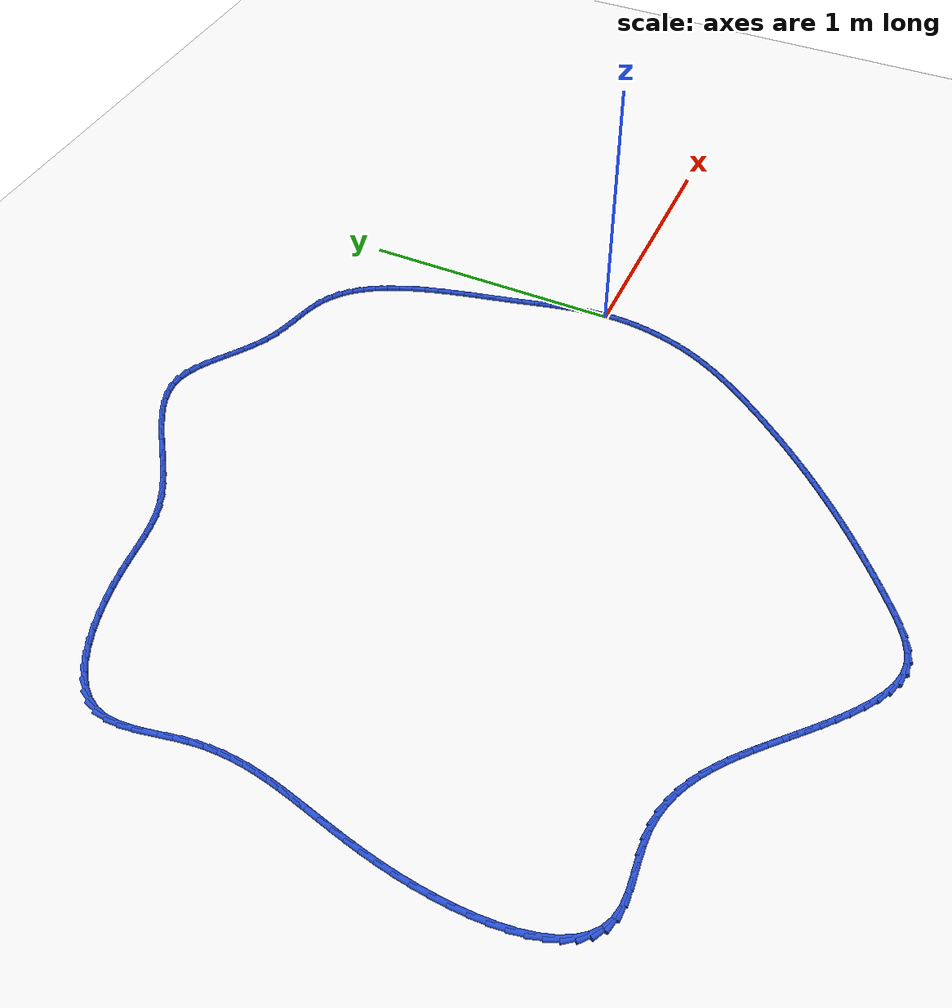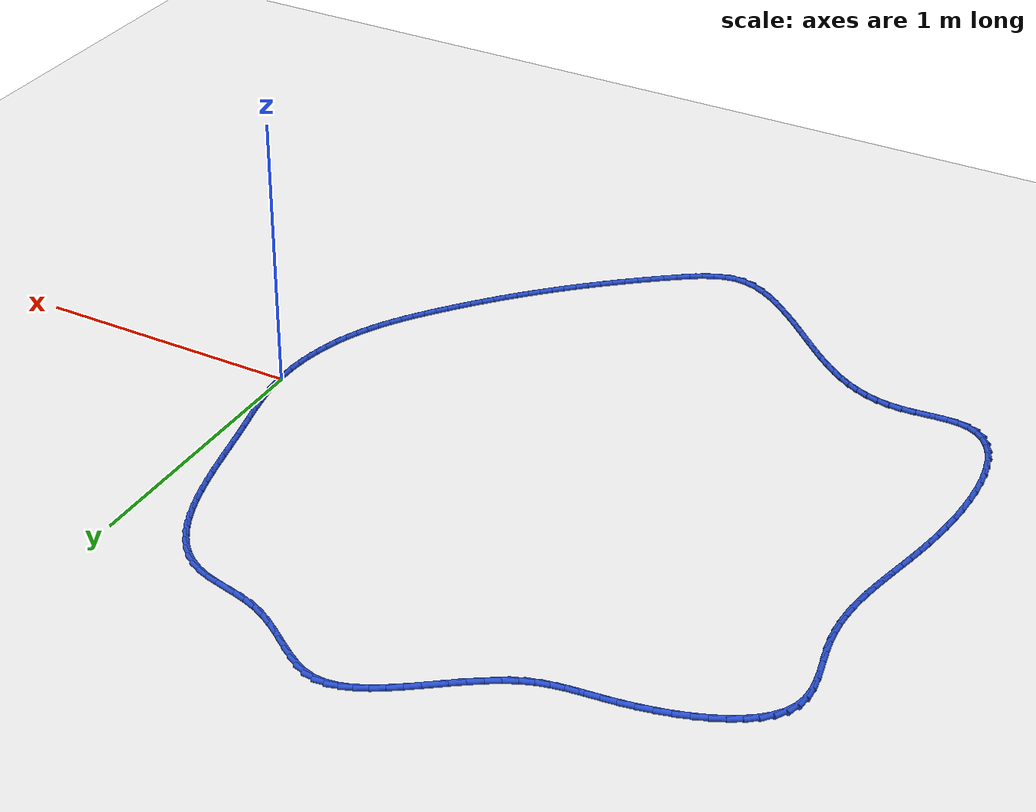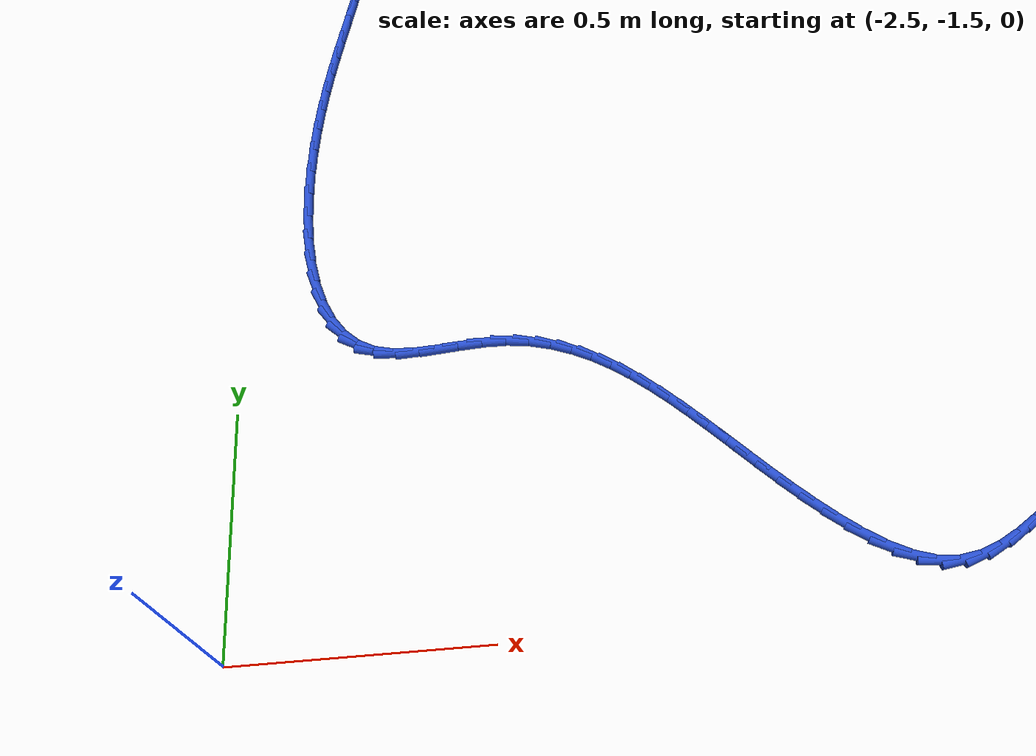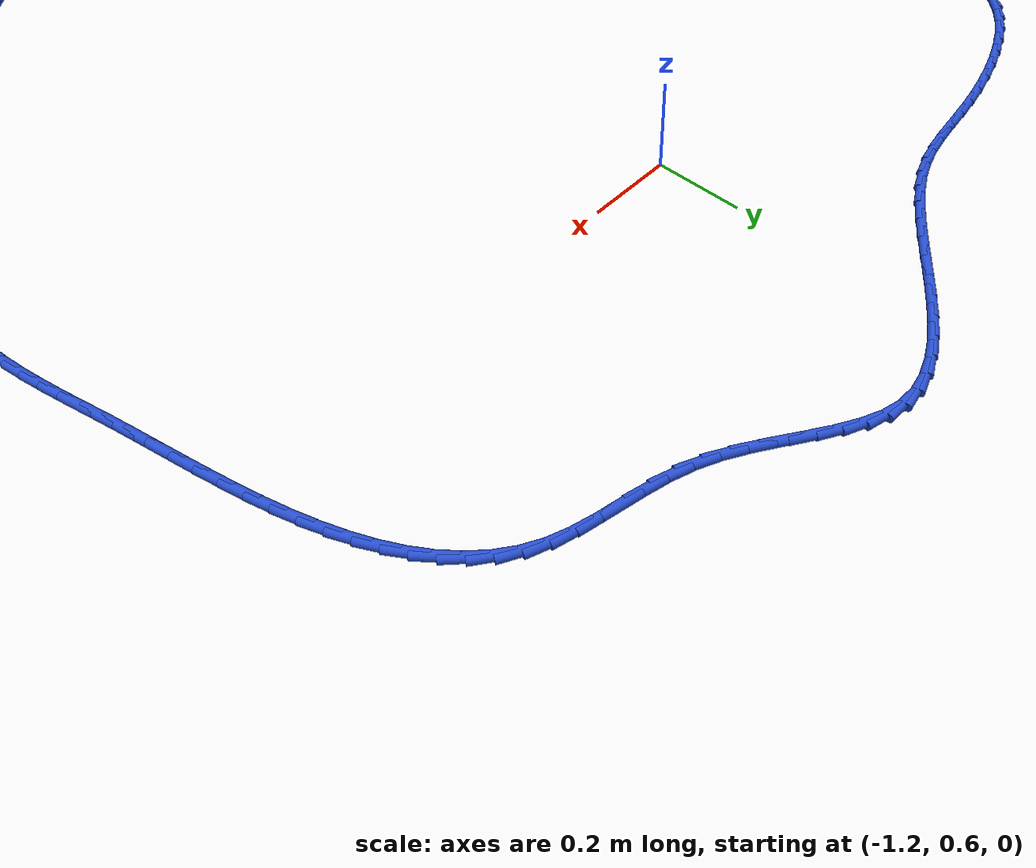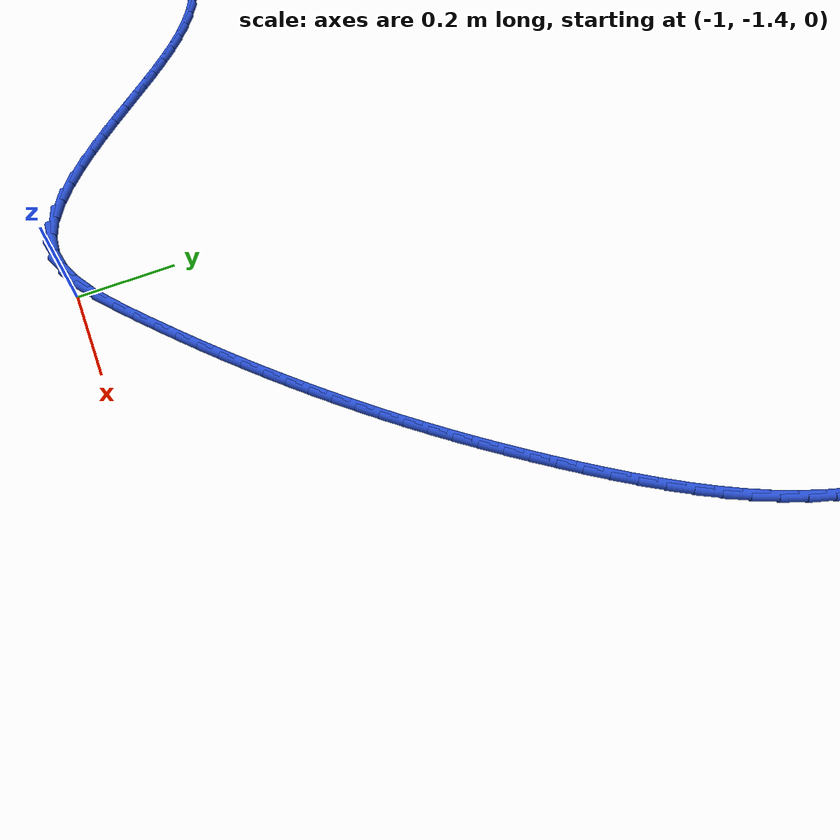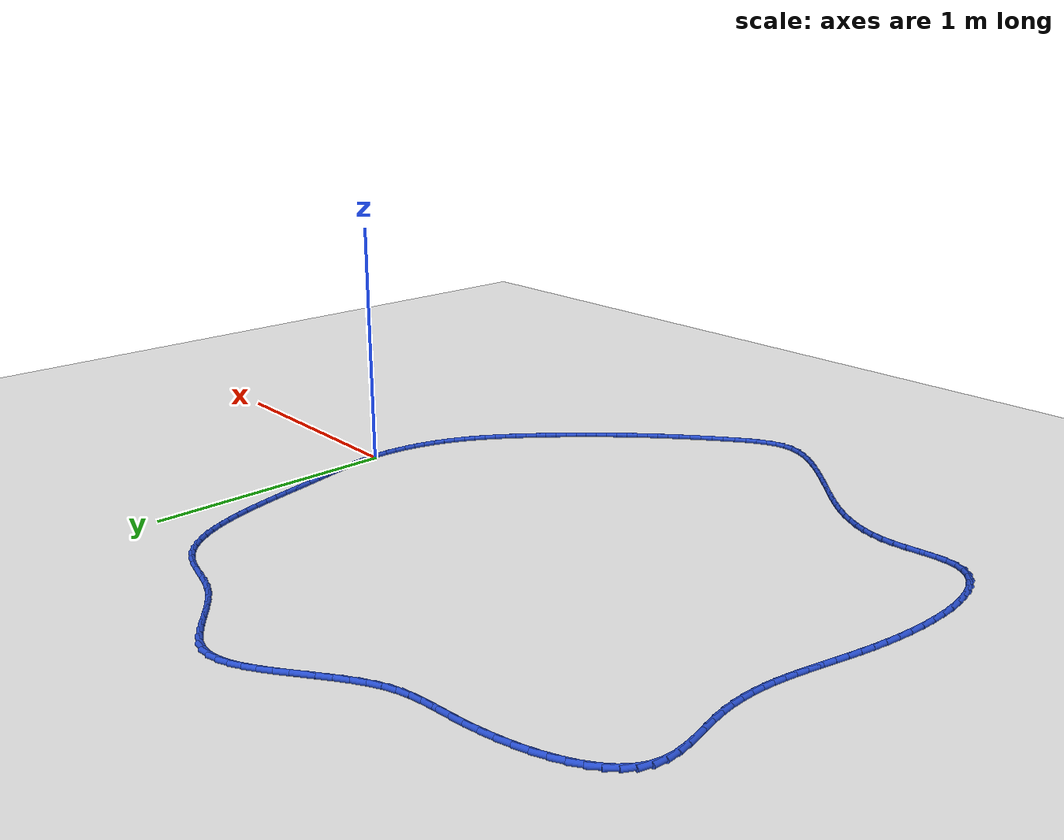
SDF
<sdf version="1.6">
 <world name="default">
  <light name="sun" type="directional">
   <pose>0 0 10 0 -0 0</pose>
   <diffuse>0.8 0.8 0.8 1</diffuse>
   <specular>0.2 0.2 0.2 1</specular>
   <attenuation>
    <range>1000</range>
    <constant>0.9</constant>
    <linear>0.01</linear>
    <quadratic>0.001</quadratic>
   </attenuation>
   <direction>-0.5 0.1 -0.9</direction>
  </light>
  <model name="ground_plane">
   <static>1</static>
   <link name="link">
    <collision name="collision">
     <geometry><plane><normal>0 0 1</normal><size>100 100</size></plane></geometry>
     <surface><friction><ode><mu>100</mu><mu2>50</mu2></ode></friction></surface>
    </collision>
    <visual name="visual">
     <cast_shadows>0</cast_shadows>
     <geometry><plane><normal>0 0 1</normal><size>100 100</size></plane></geometry>
     <material>
      <script><uri>file://media/materials/scripts/gazebo.material</uri><name>Gazebo/WhiteGlow</name></script>
     </material>
    </visual>
   </link>
  </model>
  <gravity>0 0 -9.8</gravity>
  <magnetic_field>6e-06 2.3e-05 -4.2e-05</magnetic_field>
  <atmosphere type="adiabatic"/>
  <physics name="default_physics" default="0" type="ode">
   <max_step_size>0.001</max_step_size>
   <real_time_factor>1</real_time_factor>
   <real_time_update_rate>1000</real_time_update_rate>
  </physics>
  <scene><ambient>0.4 0.4 0.4 1</ambient><background>0.7 0.7 0.7 1</background><shadows>1</shadows></scene>
  <spherical_coordinates>
   <surface_model>EARTH_WGS84</surface_model>
   <latitude_deg>0</latitude_deg>
   <longitude_deg>0</longitude_deg>
   <elevation>0</elevation>
   <heading_deg>0</heading_deg>
  </spherical_coordinates>
  <model name="line">
   <link name="link_0">
    <pose>-1.0408340855860843e-17 -4.85722573273506e-17 0.01 0 1.57 -1.5043325202332238</pose>
    <collision name="collision">
     <geometry><cylinder><radius>0.01</radius><length>0.08</length></cylinder></geometry>
    </collision>
    <visual name="visual">
     <material>
      <script><name>Gazebo/Blue</name><uri>file://media/materials/scripts/gazebo.material</uri></script>
     </material>
     <geometry><cylinder><radius>0.01</radius><length>0.08</length></cylinder></geometry>
    </visual>
   </link>
   <link name="link_1">
    <pose>-0.0030427054938025073 0.04571245630444607 0.01 0 1.57 -1.45107952147091</pose>
    <collision name="collision">
     <geometry><cylinder><radius>0.01</radius><length>0.08</length></cylinder></geometry>
    </collision>
    <visual name="visual">
     <material>
      <script><name>Gazebo/Blue</name><uri>file://media/materials/scripts/gazebo.material</uri></script>
     </material>
     <geometry><cylinder><radius>0.01</radius><length>0.08</length></cylinder></geometry>
    </visual>
   </link>
   <link name="link_2">
    <pose>-0.00849415834184347 0.09103094188991863 0.01 0 1.57 -1.407155002265236</pose>
    <collision name="collision">
     <geometry><cylinder><radius>0.01</radius><length>0.08</length></cylinder></geometry>
    </collision>
    <visual name="visual">
     <material>
      <script><name>Gazebo/Blue</name><uri>file://media/materials/scripts/gazebo.material</uri></script>
     </material>
     <geometry><cylinder><radius>0.01</radius><length>0.08</length></cylinder></geometry>
    </visual>
   </link>
   <link name="link_3">
    <pose>-0.01595622686582074 0.13622332655075753 0.01 0 1.57 -1.3732369924228394</pose>
    <collision name="collision">
     <geometry><cylinder><radius>0.01</radius><length>0.08</length></cylinder></geometry>
    </collision>
    <visual name="visual">
     <material>
      <script><name>Gazebo/Blue</name><uri>file://media/materials/scripts/gazebo.material</uri></script>
     </material>
     <geometry><cylinder><radius>0.01</radius><length>0.08</length></cylinder></geometry>
    </visual>
   </link>
   <link name="link_4">
    <pose>-0.02503077938743218 0.18155748008130265 0.01 0 1.57 -1.3495536382806632</pose>
    <collision name="collision">
     <geometry><cylinder><radius>0.01</radius><length>0.08</length></cylinder></geometry>
    </collision>
    <visual name="visual">
     <material>
      <script><name>Gazebo/Blue</name><uri>file://media/materials/scripts/gazebo.material</uri></script>
     </material>
     <geometry><cylinder><radius>0.01</radius><length>0.08</length></cylinder></geometry>
    </visual>
   </link>
   <link name="link_5">
    <pose>-0.03531968422837564 0.22730127227589397 0.01 0 1.57 -1.3359844732217534</pose>
    <collision name="collision">
     <geometry><cylinder><radius>0.01</radius><length>0.08</length></cylinder></geometry>
    </collision>
    <visual name="visual">
     <material>
      <script><name>Gazebo/Blue</name><uri>file://media/materials/scripts/gazebo.material</uri></script>
     </material>
     <geometry><cylinder><radius>0.01</radius><length>0.08</length></cylinder></geometry>
    </visual>
   </link>
   <link name="link_6">
    <pose>-0.04642480971034898 0.27372257292887126 0.01 0 1.57 -1.332155314871425</pose>
    <collision name="collision">
     <geometry><cylinder><radius>0.01</radius><length>0.08</length></cylinder></geometry>
    </collision>
    <visual name="visual">
     <material>
      <script><name>Gazebo/Blue</name><uri>file://media/materials/scripts/gazebo.material</uri></script>
     </material>
     <geometry><cylinder><radius>0.01</radius><length>0.08</length></cylinder></geometry>
    </visual>
   </link>
   <link name="link_7">
    <pose>-0.057948024155050015 0.32108925183457443 0.01 0 1.57 -1.3374973319157837</pose>
    <collision name="collision">
     <geometry><cylinder><radius>0.01</radius><length>0.08</length></cylinder></geometry>
    </collision>
    <visual name="visual">
     <material>
      <script><name>Gazebo/Blue</name><uri>file://media/materials/scripts/gazebo.material</uri></script>
     </material>
     <geometry><cylinder><radius>0.01</radius><length>0.08</length></cylinder></geometry>
    </visual>
   </link>
   <link name="link_8">
    <pose>-0.06949173861082648 0.36966860884442676 0.01 0 1.57 -1.3472967883934805</pose>
    <collision name="collision">
     <geometry><cylinder><radius>0.01</radius><length>0.08</length></cylinder></geometry>
    </collision>
    <visual name="visual">
     <material>
      <script><name>Gazebo/Blue</name><uri>file://media/materials/scripts/gazebo.material</uri></script>
     </material>
     <geometry><cylinder><radius>0.01</radius><length>0.08</length></cylinder></geometry>
    </visual>
   </link>
   <link name="link_9">
    <pose>-0.08082927268576917 0.41954846465025203 0.01 0 1.57 -1.3517249105626874</pose>
    <collision name="collision">
     <geometry><cylinder><radius>0.01</radius><length>0.08</length></cylinder></geometry>
    </collision>
    <visual name="visual">
     <material>
      <script><name>Gazebo/Blue</name><uri>file://media/materials/scripts/gazebo.material</uri></script>
     </material>
     <geometry><cylinder><radius>0.01</radius><length>0.08</length></cylinder></geometry>
    </visual>
   </link>
   <link name="link_10">
    <pose>-0.09214722640607918 0.47038263463581304 0.01 0 1.57 -1.3497383260465365</pose>
    <collision name="collision">
     <geometry><cylinder><radius>0.01</radius><length>0.08</length></cylinder></geometry>
    </collision>
    <visual name="visual">
     <material>
      <script><name>Gazebo/Blue</name><uri>file://media/materials/scripts/gazebo.material</uri></script>
     </material>
     <geometry><cylinder><radius>0.01</radius><length>0.08</length></cylinder></geometry>
    </visual>
   </link>
   <link name="link_11">
    <pose>-0.10369343362054248 0.5217606296524778 0.01 0 1.57 -1.3415094560227243</pose>
    <collision name="collision">
     <geometry><cylinder><radius>0.01</radius><length>0.08</length></cylinder></geometry>
    </collision>
    <visual name="visual">
     <material>
      <script><name>Gazebo/Blue</name><uri>file://media/materials/scripts/gazebo.material</uri></script>
     </material>
     <geometry><cylinder><radius>0.01</radius><length>0.08</length></cylinder></geometry>
    </visual>
   </link>
   <link name="link_12">
    <pose>-0.11571572817794502 0.5732719605516144 0.01 0 1.57 -1.3269629741051594</pose>
    <collision name="collision">
     <geometry><cylinder><radius>0.01</radius><length>0.08</length></cylinder></geometry>
    </collision>
    <visual name="visual">
     <material>
      <script><name>Gazebo/Blue</name><uri>file://media/materials/scripts/gazebo.material</uri></script>
     </material>
     <geometry><cylinder><radius>0.01</radius><length>0.08</length></cylinder></geometry>
    </visual>
   </link>
   <link name="link_13">
    <pose>-0.12846194392707277 0.6245061381845911 0.01 0 1.57 -1.3057866907008948</pose>
    <collision name="collision">
     <geometry><cylinder><radius>0.01</radius><length>0.08</length></cylinder></geometry>
    </collision>
    <visual name="visual">
     <material>
      <script><name>Gazebo/Blue</name><uri>file://media/materials/scripts/gazebo.material</uri></script>
     </material>
     <geometry><cylinder><radius>0.01</radius><length>0.08</length></cylinder></geometry>
    </visual>
   </link>
   <link name="link_14">
    <pose>-0.14217991471671163 0.6750526734027752 0.01 0 1.57 -1.2774289244057941</pose>
    <collision name="collision">
     <geometry><cylinder><radius>0.01</radius><length>0.08</length></cylinder></geometry>
    </collision>
    <visual name="visual">
     <material>
      <script><name>Gazebo/Blue</name><uri>file://media/materials/scripts/gazebo.material</uri></script>
     </material>
     <geometry><cylinder><radius>0.01</radius><length>0.08</length></cylinder></geometry>
    </visual>
   </link>
   <link name="link_15">
    <pose>-0.15711747439564763 0.7245010770575351 0.01 0 1.57 -1.2410873220389003</pose>
    <collision name="collision">
     <geometry><cylinder><radius>0.01</radius><length>0.08</length></cylinder></geometry>
    </collision>
    <visual name="visual">
     <material>
      <script><name>Gazebo/Blue</name><uri>file://media/materials/scripts/gazebo.material</uri></script>
     </material>
     <geometry><cylinder><radius>0.01</radius><length>0.08</length></cylinder></geometry>
    </visual>
   </link>
   <link name="link_16">
    <pose>-0.17352245681266668 0.7724408600002384 0.01 0 1.57 -1.195697009561171</pose>
    <collision name="collision">
     <geometry><cylinder><radius>0.01</radius><length>0.08</length></cylinder></geometry>
    </collision>
    <visual name="visual">
     <material>
      <script><name>Gazebo/Blue</name><uri>file://media/materials/scripts/gazebo.material</uri></script>
     </material>
     <geometry><cylinder><radius>0.01</radius><length>0.08</length></cylinder></geometry>
    </visual>
   </link>
   <link name="link_17">
    <pose>-0.19164269581655477 0.8184615330822536 0.01 0 1.57 -1.1399327570016071</pose>
    <collision name="collision">
     <geometry><cylinder><radius>0.01</radius><length>0.08</length></cylinder></geometry>
    </collision>
    <visual name="visual">
     <material>
      <script><name>Gazebo/Blue</name><uri>file://media/materials/scripts/gazebo.material</uri></script>
     </material>
     <geometry><cylinder><radius>0.01</radius><length>0.08</length></cylinder></geometry>
    </visual>
   </link>
   <link name="link_18">
    <pose>-0.2117260252560978 0.862152607154948 0.01 0 1.57 -1.0722525891120225</pose>
    <collision name="collision">
     <geometry><cylinder><radius>0.01</radius><length>0.08</length></cylinder></geometry>
    </collision>
    <visual name="visual">
     <material>
      <script><name>Gazebo/Blue</name><uri>file://media/materials/scripts/gazebo.material</uri></script>
     </material>
     <geometry><cylinder><radius>0.01</radius><length>0.08</length></cylinder></geometry>
    </visual>
   </link>
   <link name="link_19">
    <pose>-0.23402027898008168 0.9031035930696901 0.01 0 1.57 -0.9910300129629012</pose>
    <collision name="collision">
     <geometry><cylinder><radius>0.01</radius><length>0.08</length></cylinder></geometry>
    </collision>
    <visual name="visual">
     <material>
      <script><name>Gazebo/Blue</name><uri>file://media/materials/scripts/gazebo.material</uri></script>
     </material>
     <geometry><cylinder><radius>0.01</radius><length>0.08</length></cylinder></geometry>
    </visual>
   </link>
   <link name="link_20">
    <pose>-0.25877329083729256 0.9409040016778477 0.01 0 1.57 -0.8948432570262178</pose>
    <collision name="collision">
     <geometry><cylinder><radius>0.01</radius><length>0.08</length></cylinder></geometry>
    </collision>
    <visual name="visual">
     <material>
      <script><name>Gazebo/Blue</name><uri>file://media/materials/scripts/gazebo.material</uri></script>
     </material>
     <geometry><cylinder><radius>0.01</radius><length>0.08</length></cylinder></geometry>
    </visual>
   </link>
   <link name="link_21">
    <pose>-0.28623289467651625 0.9751433438307888 0.01 0 1.57 -0.7829881689887205</pose>
    <collision name="collision">
     <geometry><cylinder><radius>0.01</radius><length>0.08</length></cylinder></geometry>
    </collision>
    <visual name="visual">
     <material>
      <script><name>Gazebo/Blue</name><uri>file://media/materials/scripts/gazebo.material</uri></script>
     </material>
     <geometry><cylinder><radius>0.01</radius><length>0.08</length></cylinder></geometry>
    </visual>
   </link>
   <link name="link_22">
    <pose>-0.3166469243465387 1.0054111303798814 0.01 0 1.57 -0.6562011089389734</pose>
    <collision name="collision">
     <geometry><cylinder><radius>0.01</radius><length>0.08</length></cylinder></geometry>
    </collision>
    <visual name="visual">
     <material>
      <script><name>Gazebo/Blue</name><uri>file://media/materials/scripts/gazebo.material</uri></script>
     </material>
     <geometry><cylinder><radius>0.01</radius><length>0.08</length></cylinder></geometry>
    </visual>
   </link>
   <link name="link_23">
    <pose>-0.35026321369614594 1.0312968721764932 0.01 0 1.57 -0.5173630755354961</pose>
    <collision name="collision">
     <geometry><cylinder><radius>0.01</radius><length>0.08</length></cylinder></geometry>
    </collision>
    <visual name="visual">
     <material>
      <script><name>Gazebo/Blue</name><uri>file://media/materials/scripts/gazebo.material</uri></script>
     </material>
     <geometry><cylinder><radius>0.01</radius><length>0.08</length></cylinder></geometry>
    </visual>
   </link>
   <link name="link_24">
    <pose>-0.3873295965741239 1.0523900800719925 0.01 0 1.57 -0.3772923429703742</pose>
    <collision name="collision">
     <geometry><cylinder><radius>0.01</radius><length>0.08</length></cylinder></geometry>
    </collision>
    <visual name="visual">
     <material>
      <script><name>Gazebo/Blue</name><uri>file://media/materials/scripts/gazebo.material</uri></script>
     </material>
     <geometry><cylinder><radius>0.01</radius><length>0.08</length></cylinder></geometry>
    </visual>
   </link>
   <link name="link_25">
    <pose>-0.42798120695719294 1.0684993577329536 0.01 0 1.57 -0.2773791502655162</pose>
    <collision name="collision">
     <geometry><cylinder><radius>0.01</radius><length>0.08</length></cylinder></geometry>
    </collision>
    <visual name="visual">
     <material>
      <script><name>Gazebo/Blue</name><uri>file://media/materials/scripts/gazebo.material</uri></script>
     </material>
     <geometry><cylinder><radius>0.01</radius><length>0.08</length></cylinder></geometry>
    </visual>
   </link>
   <link name="link_26">
    <pose>-0.47159060672109976 1.0809157778415626 0.01 0 1.57 -0.22889053049434502</pose>
    <collision name="collision">
     <geometry><cylinder><radius>0.01</radius><length>0.08</length></cylinder></geometry>
    </collision>
    <visual name="visual">
     <material>
      <script><name>Gazebo/Blue</name><uri>file://media/materials/scripts/gazebo.material</uri></script>
     </material>
     <geometry><cylinder><radius>0.01</radius><length>0.08</length></cylinder></geometry>
    </visual>
   </link>
   <link name="link_27">
    <pose>-0.5172142806119906 1.09154487897848 0.01 0 1.57 -0.22626791741306163</pose>
    <collision name="collision">
     <geometry><cylinder><radius>0.01</radius><length>0.08</length></cylinder></geometry>
    </collision>
    <visual name="visual">
     <material>
      <script><name>Gazebo/Blue</name><uri>file://media/materials/scripts/gazebo.material</uri></script>
     </material>
     <geometry><cylinder><radius>0.01</radius><length>0.08</length></cylinder></geometry>
    </visual>
   </link>
   <link name="link_28">
    <pose>-0.5639076973842758 1.102294174850739 0.01 0 1.57 -0.266416799407872</pose>
    <collision name="collision">
     <geometry><cylinder><radius>0.01</radius><length>0.08</length></cylinder></geometry>
    </collision>
    <visual name="visual">
     <material>
      <script><name>Gazebo/Blue</name><uri>file://media/materials/scripts/gazebo.material</uri></script>
     </material>
     <geometry><cylinder><radius>0.01</radius><length>0.08</length></cylinder></geometry>
    </visual>
   </link>
   <link name="link_29">
    <pose>-0.6107263257923654 1.1150711791653742 0.01 0 1.57 -0.3484869038103759</pose>
    <collision name="collision">
     <geometry><cylinder><radius>0.01</radius><length>0.08</length></cylinder></geometry>
    </collision>
    <visual name="visual">
     <material>
      <script><name>Gazebo/Blue</name><uri>file://media/materials/scripts/gazebo.material</uri></script>
     </material>
     <geometry><cylinder><radius>0.01</radius><length>0.08</length></cylinder></geometry>
    </visual>
   </link>
   <link name="link_30">
    <pose>-0.6567256345906695 1.1317834056294187 0.01 0 1.57 -0.4598449138621373</pose>
    <collision name="collision">
     <geometry><cylinder><radius>0.01</radius><length>0.08</length></cylinder></geometry>
    </collision>
    <visual name="visual">
     <material>
      <script><name>Gazebo/Blue</name><uri>file://media/materials/scripts/gazebo.material</uri></script>
     </material>
     <geometry><cylinder><radius>0.01</radius><length>0.08</length></cylinder></geometry>
    </visual>
   </link>
   <link name="link_31">
    <pose>-0.7011395254266316 1.1537796350675653 0.01 0 1.57 -0.5468872597294228</pose>
    <collision name="collision">
     <geometry><cylinder><radius>0.01</radius><length>0.08</length></cylinder></geometry>
    </collision>
    <visual name="visual">
     <material>
      <script><name>Gazebo/Blue</name><uri>file://media/materials/scripts/gazebo.material</uri></script>
     </material>
     <geometry><cylinder><radius>0.01</radius><length>0.08</length></cylinder></geometry>
    </visual>
   </link>
   <link name="link_32">
    <pose>-0.7440093925834049 1.1798801196226523 0.01 0 1.57 -0.5975890508575826</pose>
    <collision name="collision">
     <geometry><cylinder><radius>0.01</radius><length>0.08</length></cylinder></geometry>
    </collision>
    <visual name="visual">
     <material>
      <script><name>Gazebo/Blue</name><uri>file://media/materials/scripts/gazebo.material</uri></script>
     </material>
     <geometry><cylinder><radius>0.01</radius><length>0.08</length></cylinder></geometry>
    </visual>
   </link>
   <link name="link_33">
    <pose>-0.7856049434894453 1.2081901868539202 0.01 0 1.57 -0.6142105241046814</pose>
    <collision name="collision">
     <geometry><cylinder><radius>0.01</radius><length>0.08</length></cylinder></geometry>
    </collision>
    <visual name="visual">
     <material>
      <script><name>Gazebo/Blue</name><uri>file://media/materials/scripts/gazebo.material</uri></script>
     </material>
     <geometry><cylinder><radius>0.01</radius><length>0.08</length></cylinder></geometry>
    </visual>
   </link>
   <link name="link_34">
    <pose>-0.826195899625606 1.23681512031787 0.01 0 1.57 -0.5961971515108322</pose>
    <collision name="collision">
     <geometry><cylinder><radius>0.01</radius><length>0.08</length></cylinder></geometry>
    </collision>
    <visual name="visual">
     <material>
      <script><name>Gazebo/Blue</name><uri>file://media/materials/scripts/gazebo.material</uri></script>
     </material>
     <geometry><cylinder><radius>0.01</radius><length>0.08</length></cylinder></geometry>
    </visual>
   </link>
   <link name="link_35">
    <pose>-0.8660519824727396 1.2638602035710034 0.01 0 1.57 -0.5392231969492912</pose>
    <collision name="collision">
     <geometry><cylinder><radius>0.01</radius><length>0.08</length></cylinder></geometry>
    </collision>
    <visual name="visual">
     <material>
      <script><name>Gazebo/Blue</name><uri>file://media/materials/scripts/gazebo.material</uri></script>
     </material>
     <geometry><cylinder><radius>0.01</radius><length>0.08</length></cylinder></geometry>
    </visual>
   </link>
   <link name="link_36">
    <pose>-0.9054429135116993 1.2874307201698223 0.01 0 1.57 -0.43473994715595793</pose>
    <collision name="collision">
     <geometry><cylinder><radius>0.01</radius><length>0.08</length></cylinder></geometry>
    </collision>
    <visual name="visual">
     <material>
      <script><name>Gazebo/Blue</name><uri>file://media/materials/scripts/gazebo.material</uri></script>
     </material>
     <geometry><cylinder><radius>0.01</radius><length>0.08</length></cylinder></geometry>
    </visual>
   </link>
   <link name="link_37">
    <pose>-0.9446384142233379 1.3056319536708278 0.01 0 1.57 -0.27163131892643644</pose>
    <collision name="collision">
     <geometry><cylinder><radius>0.01</radius><length>0.08</length></cylinder></geometry>
    </collision>
    <visual name="visual">
     <material>
      <script><name>Gazebo/Blue</name><uri>file://media/materials/scripts/gazebo.material</uri></script>
     </material>
     <geometry><cylinder><radius>0.01</radius><length>0.08</length></cylinder></geometry>
    </visual>
   </link>
   <link name="link_38">
    <pose>-0.9839082060885083 1.3165691876305219 0.01 0 1.57 -0.05703351998115613</pose>
    <collision name="collision">
     <geometry><cylinder><radius>0.01</radius><length>0.08</length></cylinder></geometry>
    </collision>
    <visual name="visual">
     <material>
      <script><name>Gazebo/Blue</name><uri>file://media/materials/scripts/gazebo.material</uri></script>
     </material>
     <geometry><cylinder><radius>0.01</radius><length>0.08</length></cylinder></geometry>
    </visual>
   </link>
   <link name="link_39">
    <pose>-1.0234781739367724 1.3188284523761604 0.01 0 1.57 0.14503146356662466</pose>
    <collision name="collision">
     <geometry><cylinder><radius>0.01</radius><length>0.08</length></cylinder></geometry>
    </collision>
    <visual name="visual">
     <material>
      <script><name>Gazebo/Blue</name><uri>file://media/materials/scripts/gazebo.material</uri></script>
     </material>
     <geometry><cylinder><radius>0.01</radius><length>0.08</length></cylinder></geometry>
    </visual>
   </link>
   <link name="link_40">
    <pose>-1.063391555785844 1.3129988250553801 0.01 0 1.57 0.3080580746111416</pose>
    <collision name="collision">
     <geometry><cylinder><radius>0.01</radius><length>0.08</length></cylinder></geometry>
    </collision>
    <visual name="visual">
     <material>
      <script><name>Gazebo/Blue</name><uri>file://media/materials/scripts/gazebo.material</uri></script>
     </material>
     <geometry><cylinder><radius>0.01</radius><length>0.08</length></cylinder></geometry>
    </visual>
   </link>
   <link name="link_41">
    <pose>-1.1036440275535844 1.3001909857494907 0.01 0 1.57 0.4312453069823611</pose>
    <collision name="collision">
     <geometry><cylinder><radius>0.01</radius><length>0.08</length></cylinder></geometry>
    </collision>
    <visual name="visual">
     <material>
      <script><name>Gazebo/Blue</name><uri>file://media/materials/scripts/gazebo.material</uri></script>
     </material>
     <geometry><cylinder><radius>0.01</radius><length>0.08</length></cylinder></geometry>
    </visual>
   </link>
   <link name="link_42">
    <pose>-1.1442312650430837 1.2815156157984304 0.01 0 1.57 0.5200794726018029</pose>
    <collision name="collision">
     <geometry><cylinder><radius>0.01</radius><length>0.08</length></cylinder></geometry>
    </collision>
    <visual name="visual">
     <material>
      <script><name>Gazebo/Blue</name><uri>file://media/materials/scripts/gazebo.material</uri></script>
     </material>
     <geometry><cylinder><radius>0.01</radius><length>0.08</length></cylinder></geometry>
    </visual>
   </link>
   <link name="link_43">
    <pose>-1.1851489440574348 1.2580833965421379 0.01 0 1.57 0.5809621670062222</pose>
    <collision name="collision">
     <geometry><cylinder><radius>0.01</radius><length>0.08</length></cylinder></geometry>
    </collision>
    <visual name="visual">
     <material>
      <script><name>Gazebo/Blue</name><uri>file://media/materials/scripts/gazebo.material</uri></script>
     </material>
     <geometry><cylinder><radius>0.01</radius><length>0.08</length></cylinder></geometry>
    </visual>
   </link>
   <link name="link_44">
    <pose>-1.226392740399729 1.2310050093205518 0.01 0 1.57 0.6190403841027216</pose>
    <collision name="collision">
     <geometry><cylinder><radius>0.01</radius><length>0.08</length></cylinder></geometry>
    </collision>
    <visual name="visual">
     <material>
      <script><name>Gazebo/Blue</name><uri>file://media/materials/scripts/gazebo.material</uri></script>
     </material>
     <geometry><cylinder><radius>0.01</radius><length>0.08</length></cylinder></geometry>
    </visual>
   </link>
   <link name="link_45">
    <pose>-1.2679583298730592 1.2013911354736106 0.01 0 1.57 0.6377675494994247</pose>
    <collision name="collision">
     <geometry><cylinder><radius>0.01</radius><length>0.08</length></cylinder></geometry>
    </collision>
    <visual name="visual">
     <material>
      <script><name>Gazebo/Blue</name><uri>file://media/materials/scripts/gazebo.material</uri></script>
     </material>
     <geometry><cylinder><radius>0.01</radius><length>0.08</length></cylinder></geometry>
    </visual>
   </link>
   <link name="link_46">
    <pose>-1.3098413882805162 1.170352456341253 0.01 0 1.57 0.639021673335138</pose>
    <collision name="collision">
     <geometry><cylinder><radius>0.01</radius><length>0.08</length></cylinder></geometry>
    </collision>
    <visual name="visual">
     <material>
      <script><name>Gazebo/Blue</name><uri>file://media/materials/scripts/gazebo.material</uri></script>
     </material>
     <geometry><cylinder><radius>0.01</radius><length>0.08</length></cylinder></geometry>
    </visual>
   </link>
   <link name="link_47">
    <pose>-1.3520375914251934 1.1389996532634172 0.01 0 1.57 0.6232886761222403</pose>
    <collision name="collision">
     <geometry><cylinder><radius>0.01</radius><length>0.08</length></cylinder></geometry>
    </collision>
    <visual name="visual">
     <material>
      <script><name>Gazebo/Blue</name><uri>file://media/materials/scripts/gazebo.material</uri></script>
     </material>
     <geometry><cylinder><radius>0.01</radius><length>0.08</length></cylinder></geometry>
    </visual>
   </link>
   <link name="link_48">
    <pose>-1.394542615110181 1.1084434075800425 0.01 0 1.57 0.5897685352727546</pose>
    <collision name="collision">
     <geometry><cylinder><radius>0.01</radius><length>0.08</length></cylinder></geometry>
    </collision>
    <visual name="visual">
     <material>
      <script><name>Gazebo/Blue</name><uri>file://media/materials/scripts/gazebo.material</uri></script>
     </material>
     <geometry><cylinder><radius>0.01</radius><length>0.08</length></cylinder></geometry>
    </visual>
   </link>
   <link name="link_49">
    <pose>-1.4373521351385719 1.079794400631067 0.01 0 1.57 0.5364062704053323</pose>
    <collision name="collision">
     <geometry><cylinder><radius>0.01</radius><length>0.08</length></cylinder></geometry>
    </collision>
    <visual name="visual">
     <material>
      <script><name>Gazebo/Blue</name><uri>file://media/materials/scripts/gazebo.material</uri></script>
     </material>
     <geometry><cylinder><radius>0.01</radius><length>0.08</length></cylinder></geometry>
    </visual>
   </link>
   <link name="link_50">
    <pose>-1.4804618273134582 1.0541633137564288 0.01 0 1.57 0.4599493891614489</pose>
    <collision name="collision">
     <geometry><cylinder><radius>0.01</radius><length>0.08</length></cylinder></geometry>
    </collision>
    <visual name="visual">
     <material>
      <script><name>Gazebo/Blue</name><uri>file://media/materials/scripts/gazebo.material</uri></script>
     </material>
     <geometry><cylinder><radius>0.01</radius><length>0.08</length></cylinder></geometry>
    </visual>
   </link>
   <link name="link_51">
    <pose>-1.5238673674379313 1.032660828296068 0.01 0 1.57 0.3579654578195431</pose>
    <collision name="collision">
     <geometry><cylinder><radius>0.01</radius><length>0.08</length></cylinder></geometry>
    </collision>
    <visual name="visual">
     <material>
      <script><name>Gazebo/Blue</name><uri>file://media/materials/scripts/gazebo.material</uri></script>
     </material>
     <geometry><cylinder><radius>0.01</radius><length>0.08</length></cylinder></geometry>
    </visual>
   </link>
   <link name="link_52">
    <pose>-1.5675752768028692 1.0163104935056506 0.01 0 1.57 0.25476808881046115</pose>
    <collision name="collision">
     <geometry><cylinder><radius>0.01</radius><length>0.08</length></cylinder></geometry>
    </collision>
    <visual name="visual">
     <material>
      <script><name>Gazebo/Blue</name><uri>file://media/materials/scripts/gazebo.material</uri></script>
     </material>
     <geometry><cylinder><radius>0.01</radius><length>0.08</length></cylinder></geometry>
    </visual>
   </link>
   <link name="link_53">
    <pose>-1.6117578360056053 1.004804157001896 0.01 0 1.57 0.17631539324810577</pose>
    <collision name="collision">
     <geometry><cylinder><radius>0.01</radius><length>0.08</length></cylinder></geometry>
    </collision>
    <visual name="visual">
     <material>
      <script><name>Gazebo/Blue</name><uri>file://media/materials/scripts/gazebo.material</uri></script>
     </material>
     <geometry><cylinder><radius>0.01</radius><length>0.08</length></cylinder></geometry>
    </visual>
   </link>
   <link name="link_54">
    <pose>-1.6567167303829393 0.9967940354612354 0.01 0 1.57 0.12722478906380533</pose>
    <collision name="collision">
     <geometry><cylinder><radius>0.01</radius><length>0.08</length></cylinder></geometry>
    </collision>
    <visual name="visual">
     <material>
      <script><name>Gazebo/Blue</name><uri>file://media/materials/scripts/gazebo.material</uri></script>
     </material>
     <geometry><cylinder><radius>0.01</radius><length>0.08</length></cylinder></geometry>
    </visual>
   </link>
   <link name="link_55">
    <pose>-1.702757079837194 0.9909047524394918 0.01 0 1.57 0.10803553216902584</pose>
    <collision name="collision">
     <geometry><cylinder><radius>0.01</radius><length>0.08</length></cylinder></geometry>
    </collision>
    <visual name="visual">
     <material>
      <script><name>Gazebo/Blue</name><uri>file://media/materials/scripts/gazebo.material</uri></script>
     </material>
     <geometry><cylinder><radius>0.01</radius><length>0.08</length></cylinder></geometry>
    </visual>
   </link>
   <link name="link_56">
    <pose>-1.7501840042706907 0.9857609314924872 0.01 0 1.57 0.11700982912704051</pose>
    <collision name="collision">
     <geometry><cylinder><radius>0.01</radius><length>0.08</length></cylinder></geometry>
    </collision>
    <visual name="visual">
     <material>
      <script><name>Gazebo/Blue</name><uri>file://media/materials/scripts/gazebo.material</uri></script>
     </material>
     <geometry><cylinder><radius>0.01</radius><length>0.08</length></cylinder></geometry>
    </visual>
   </link>
   <link name="link_57">
    <pose>-1.7993026235857505 0.9799871961760432 0.01 0 1.57 0.14953764125680877</pose>
    <collision name="collision">
     <geometry><cylinder><radius>0.01</radius><length>0.08</length></cylinder></geometry>
    </collision>
    <visual name="visual">
     <material>
      <script><name>Gazebo/Blue</name><uri>file://media/materials/scripts/gazebo.material</uri></script>
     </material>
     <geometry><cylinder><radius>0.01</radius><length>0.08</length></cylinder></geometry>
    </visual>
   </link>
   <link name="link_58">
    <pose>-1.8503232030662449 0.9723003167325845 0.01 0 1.57 0.1907710073906245</pose>
    <collision name="collision">
     <geometry><cylinder><radius>0.01</radius><length>0.08</length></cylinder></geometry>
    </collision>
    <visual name="visual">
     <material>
      <script><name>Gazebo/Blue</name><uri>file://media/materials/scripts/gazebo.material</uri></script>
     </material>
     <geometry><cylinder><radius>0.01</radius><length>0.08</length></cylinder></geometry>
    </visual>
   </link>
   <link name="link_59">
    <pose>-1.902656511900261 0.9621937352986513 0.01 0 1.57 0.23565278258140304</pose>
    <collision name="collision">
     <geometry><cylinder><radius>0.01</radius><length>0.08</length></cylinder></geometry>
    </collision>
    <visual name="visual">
     <material>
      <script><name>Gazebo/Blue</name><uri>file://media/materials/scripts/gazebo.material</uri></script>
     </material>
     <geometry><cylinder><radius>0.01</radius><length>0.08</length></cylinder></geometry>
    </visual>
   </link>
   <link name="link_60">
    <pose>-1.955312467155676 0.9495503025108446 0.01 0 1.57 0.2861339120182787</pose>
    <collision name="collision">
     <geometry><cylinder><radius>0.01</radius><length>0.08</length></cylinder></geometry>
    </collision>
    <visual name="visual">
     <material>
      <script><name>Gazebo/Blue</name><uri>file://media/materials/scripts/gazebo.material</uri></script>
     </material>
     <geometry><cylinder><radius>0.01</radius><length>0.08</length></cylinder></geometry>
    </visual>
   </link>
   <link name="link_61">
    <pose>-2.0072979822817025 0.9342557868764225 0.01 0 1.57 0.3445685625059265</pose>
    <collision name="collision">
     <geometry><cylinder><radius>0.01</radius><length>0.08</length></cylinder></geometry>
    </collision>
    <visual name="visual">
     <material>
      <script><name>Gazebo/Blue</name><uri>file://media/materials/scripts/gazebo.material</uri></script>
     </material>
     <geometry><cylinder><radius>0.01</radius><length>0.08</length></cylinder></geometry>
    </visual>
   </link>
   <link name="link_62">
    <pose>-2.057619970727552 0.916195956902642 0.01 0 1.57 0.41391984843091195</pose>
    <collision name="collision">
     <geometry><cylinder><radius>0.01</radius><length>0.08</length></cylinder></geometry>
    </collision>
    <visual name="visual">
     <material>
      <script><name>Gazebo/Blue</name><uri>file://media/materials/scripts/gazebo.material</uri></script>
     </material>
     <geometry><cylinder><radius>0.01</radius><length>0.08</length></cylinder></geometry>
    </visual>
   </link>
   <link name="link_63">
    <pose>-2.1052853459424368 0.8952565810967607 0.01 0 1.57 0.49802559149440073</pose>
    <collision name="collision">
     <geometry><cylinder><radius>0.01</radius><length>0.08</length></cylinder></geometry>
    </collision>
    <visual name="visual">
     <material>
      <script><name>Gazebo/Blue</name><uri>file://media/materials/scripts/gazebo.material</uri></script>
     </material>
     <geometry><cylinder><radius>0.01</radius><length>0.08</length></cylinder></geometry>
    </visual>
   </link>
   <link name="link_64">
    <pose>-2.149301021375569 0.8713234279660362 0.01 0 1.57 0.6018094727072582</pose>
    <collision name="collision">
     <geometry><cylinder><radius>0.01</radius><length>0.08</length></cylinder></geometry>
    </collision>
    <visual name="visual">
     <material>
      <script><name>Gazebo/Blue</name><uri>file://media/materials/scripts/gazebo.material</uri></script>
     </material>
     <geometry><cylinder><radius>0.01</radius><length>0.08</length></cylinder></geometry>
    </visual>
   </link>
   <link name="link_65">
    <pose>-2.1886739104761617 0.8442822660177258 0.01 0 1.57 0.7311764997715887</pose>
    <collision name="collision">
     <geometry><cylinder><radius>0.01</radius><length>0.08</length></cylinder></geometry>
    </collision>
    <visual name="visual">
     <material>
      <script><name>Gazebo/Blue</name><uri>file://media/materials/scripts/gazebo.material</uri></script>
     </material>
     <geometry><cylinder><radius>0.01</radius><length>0.08</length></cylinder></geometry>
    </visual>
   </link>
   <link name="link_66">
    <pose>-2.2224109266934278 0.8140188637590867 0.01 0 1.57 0.8919285727185258</pose>
    <collision name="collision">
     <geometry><cylinder><radius>0.01</radius><length>0.08</length></cylinder></geometry>
    </collision>
    <visual name="visual">
     <material>
      <script><name>Gazebo/Blue</name><uri>file://media/materials/scripts/gazebo.material</uri></script>
     </material>
     <geometry><cylinder><radius>0.01</radius><length>0.08</length></cylinder></geometry>
    </visual>
   </link>
   <link name="link_67">
    <pose>-2.2495189834765776 0.7804189896973772 0.01 0 1.57 1.086620536200083</pose>
    <collision name="collision">
     <geometry><cylinder><radius>0.01</radius><length>0.08</length></cylinder></geometry>
    </collision>
    <visual name="visual">
     <material>
      <script><name>Gazebo/Blue</name><uri>file://media/materials/scripts/gazebo.material</uri></script>
     </material>
     <geometry><cylinder><radius>0.01</radius><length>0.08</length></cylinder></geometry>
    </visual>
   </link>
   <link name="link_68">
    <pose>-2.2690049942748254 0.7433684123398537 0.01 0 1.57 1.3081487789885176</pose>
    <collision name="collision">
     <geometry><cylinder><radius>0.01</radius><length>0.08</length></cylinder></geometry>
    </collision>
    <visual name="visual">
     <material>
      <script><name>Gazebo/Blue</name><uri>file://media/materials/scripts/gazebo.material</uri></script>
     </material>
     <geometry><cylinder><radius>0.01</radius><length>0.08</length></cylinder></geometry>
    </visual>
   </link>
   <link name="link_69">
    <pose>-2.2799210561690058 0.702766892418842 0.01 0 1.57 1.5079635726277851</pose>
    <collision name="collision">
     <geometry><cylinder><radius>0.01</radius><length>0.08</length></cylinder></geometry>
    </collision>
    <visual name="visual">
     <material>
      <script><name>Gazebo/Blue</name><uri>file://media/materials/scripts/gazebo.material</uri></script>
     </material>
     <geometry><cylinder><radius>0.01</radius><length>0.08</length></cylinder></geometry>
    </visual>
   </link>
   <link name="link_70">
    <pose>-2.2826787528451837 0.6589351891980656 0.01 0 1.57 -1.4969184186341356</pose>
    <collision name="collision">
     <geometry><cylinder><radius>0.01</radius><length>0.08</length></cylinder></geometry>
    </collision>
    <visual name="visual">
     <material>
      <script><name>Gazebo/Blue</name><uri>file://media/materials/scripts/gazebo.material</uri></script>
     </material>
     <geometry><cylinder><radius>0.01</radius><length>0.08</length></cylinder></geometry>
    </visual>
   </link>
   <link name="link_71">
    <pose>-2.2792552018156145 0.612678868072581 0.01 0 1.57 -1.4144799752195978</pose>
    <collision name="collision">
     <geometry><cylinder><radius>0.01</radius><length>0.08</length></cylinder></geometry>
    </collision>
    <visual name="visual">
     <material>
      <script><name>Gazebo/Blue</name><uri>file://media/materials/scripts/gazebo.material</uri></script>
     </material>
     <geometry><cylinder><radius>0.01</radius><length>0.08</length></cylinder></geometry>
    </visual>
   </link>
   <link name="link_72">
    <pose>-2.2717141711036164 0.5648303279036696 0.01 0 1.57 -1.3759128625830233</pose>
    <collision name="collision">
     <geometry><cylinder><radius>0.01</radius><length>0.08</length></cylinder></geometry>
    </collision>
    <visual name="visual">
     <material>
      <script><name>Gazebo/Blue</name><uri>file://media/materials/scripts/gazebo.material</uri></script>
     </material>
     <geometry><cylinder><radius>0.01</radius><length>0.08</length></cylinder></geometry>
    </visual>
   </link>
   <link name="link_73">
    <pose>-2.262119428732507 0.5162219675526116 0.01 0 1.57 -1.3758281898802402</pose>
    <collision name="collision">
     <geometry><cylinder><radius>0.01</radius><length>0.08</length></cylinder></geometry>
    </collision>
    <visual name="visual">
     <material>
      <script><name>Gazebo/Blue</name><uri>file://media/materials/scripts/gazebo.material</uri></script>
     </material>
     <geometry><cylinder><radius>0.01</radius><length>0.08</length></cylinder></geometry>
    </visual>
   </link>
   <link name="link_74">
    <pose>-2.252534742725607 0.46768618588068717 0.01 0 1.57 -1.4139658285064758</pose>
    <collision name="collision">
     <geometry><cylinder><radius>0.01</radius><length>0.08</length></cylinder></geometry>
    </collision>
    <visual name="visual">
     <material>
      <script><name>Gazebo/Blue</name><uri>file://media/materials/scripts/gazebo.material</uri></script>
     </material>
     <geometry><cylinder><radius>0.01</radius><length>0.08</length></cylinder></geometry>
    </visual>
   </link>
   <link name="link_75">
    <pose>-2.245001297897707 0.42004507217768966 0.01 0 1.57 -1.4761943900437773</pose>
    <collision name="collision">
     <geometry><cylinder><radius>0.01</radius><length>0.08</length></cylinder></geometry>
    </collision>
    <visual name="visual">
     <material>
      <script><name>Gazebo/Blue</name><uri>file://media/materials/scripts/gazebo.material</uri></script>
     </material>
     <geometry><cylinder><radius>0.01</radius><length>0.08</length></cylinder></geometry>
    </visual>
   </link>
   <link name="link_76">
    <pose>-2.240602259726956 0.37368336561871796 0.01 0 1.57 -1.538251700057381</pose>
    <collision name="collision">
     <geometry><cylinder><radius>0.01</radius><length>0.08</length></cylinder></geometry>
    </collision>
    <visual name="visual">
     <material>
      <script><name>Gazebo/Blue</name><uri>file://media/materials/scripts/gazebo.material</uri></script>
     </material>
     <geometry><cylinder><radius>0.01</radius><length>0.08</length></cylinder></geometry>
    </visual>
   </link>
   <link name="link_77">
    <pose>-2.239127864552394 0.3283955639446485 0.01 0 1.57 1.5449587053893048</pose>
    <collision name="collision">
     <geometry><cylinder><radius>0.01</radius><length>0.08</length></cylinder></geometry>
    </collision>
    <visual name="visual">
     <material>
      <script><name>Gazebo/Blue</name><uri>file://media/materials/scripts/gazebo.material</uri></script>
     </material>
     <geometry><cylinder><radius>0.01</radius><length>0.08</length></cylinder></geometry>
    </visual>
   </link>
   <link name="link_78">
    <pose>-2.240276890641112 0.2839344129225451 0.01 0 1.57 1.49185663152797</pose>
    <collision name="collision">
     <geometry><cylinder><radius>0.01</radius><length>0.08</length></cylinder></geometry>
    </collision>
    <visual name="visual">
     <material>
      <script><name>Gazebo/Blue</name><uri>file://media/materials/scripts/gazebo.material</uri></script>
     </material>
     <geometry><cylinder><radius>0.01</radius><length>0.08</length></cylinder></geometry>
    </visual>
   </link>
   <link name="link_79">
    <pose>-2.243748116260204 0.2400526583194699 0.01 0 1.57 1.4453449018778282</pose>
    <collision name="collision">
     <geometry><cylinder><radius>0.01</radius><length>0.08</length></cylinder></geometry>
    </collision>
    <visual name="visual">
     <material>
      <script><name>Gazebo/Blue</name><uri>file://media/materials/scripts/gazebo.material</uri></script>
     </material>
     <geometry><cylinder><radius>0.01</radius><length>0.08</length></cylinder></geometry>
    </visual>
   </link>
   <link name="link_80">
    <pose>-2.24924031967676 0.19650304590248666 0.01 0 1.57 1.4063676767059676</pose>
    <collision name="collision">
     <geometry><cylinder><radius>0.01</radius><length>0.08</length></cylinder></geometry>
    </collision>
    <visual name="visual">
     <material>
      <script><name>Gazebo/Blue</name><uri>file://media/materials/scripts/gazebo.material</uri></script>
     </material>
     <geometry><cylinder><radius>0.01</radius><length>0.08</length></cylinder></geometry>
    </visual>
   </link>
   <link name="link_81">
    <pose>-2.2564522791578727 0.15303832143865798 0.01 0 1.57 1.3754937663213318</pose>
    <collision name="collision">
     <geometry><cylinder><radius>0.01</radius><length>0.08</length></cylinder></geometry>
    </collision>
    <visual name="visual">
     <material>
      <script><name>Gazebo/Blue</name><uri>file://media/materials/scripts/gazebo.material</uri></script>
     </material>
     <geometry><cylinder><radius>0.01</radius><length>0.08</length></cylinder></geometry>
    </visual>
   </link>
   <link name="link_82">
    <pose>-2.2650827729706347 0.1094112306950465 0.01 0 1.57 1.352952641293258</pose>
    <collision name="collision">
     <geometry><cylinder><radius>0.01</radius><length>0.08</length></cylinder></geometry>
    </collision>
    <visual name="visual">
     <material>
      <script><name>Gazebo/Blue</name><uri>file://media/materials/scripts/gazebo.material</uri></script>
     </material>
     <geometry><cylinder><radius>0.01</radius><length>0.08</length></cylinder></geometry>
    </visual>
   </link>
   <link name="link_83">
    <pose>-2.274830579382137 0.06537451943871617 0.01 0 1.57 1.3386933624595787</pose>
    <collision name="collision">
     <geometry><cylinder><radius>0.01</radius><length>0.08</length></cylinder></geometry>
    </collision>
    <visual name="visual">
     <material>
      <script><name>Gazebo/Blue</name><uri>file://media/materials/scripts/gazebo.material</uri></script>
     </material>
     <geometry><cylinder><radius>0.01</radius><length>0.08</length></cylinder></geometry>
    </visual>
   </link>
   <link name="link_84">
    <pose>-2.2853944766594716 0.020680933436728936 0.01 0 1.57 1.3324472859616119</pose>
    <collision name="collision">
     <geometry><cylinder><radius>0.01</radius><length>0.08</length></cylinder></geometry>
    </collision>
    <visual name="visual">
     <material>
      <script><name>Gazebo/Blue</name><uri>file://media/materials/scripts/gazebo.material</uri></script>
     </material>
     <geometry><cylinder><radius>0.01</radius><length>0.08</length></cylinder></geometry>
    </visual>
   </link>
   <link name="link_85">
    <pose>-2.296473243069731 -0.024916781543851213 0.01 0 1.57 1.3337828613807026</pose>
    <collision name="collision">
     <geometry><cylinder><radius>0.01</radius><length>0.08</length></cylinder></geometry>
    </collision>
    <visual name="visual">
     <material>
      <script><name>Gazebo/Blue</name><uri>file://media/materials/scripts/gazebo.material</uri></script>
     </material>
     <geometry><cylinder><radius>0.01</radius><length>0.08</length></cylinder></geometry>
    </visual>
   </link>
   <link name="link_86">
    <pose>-2.307765656880007 -0.07166587973596174 0.01 0 1.57 1.342148138289531</pose>
    <collision name="collision">
     <geometry><cylinder><radius>0.01</radius><length>0.08</length></cylinder></geometry>
    </collision>
    <visual name="visual">
     <material>
      <script><name>Gazebo/Blue</name><uri>file://media/materials/scripts/gazebo.material</uri></script>
     </material>
     <geometry><cylinder><radius>0.01</radius><length>0.08</length></cylinder></geometry>
    </visual>
   </link>
   <link name="link_87">
    <pose>-2.3189704963573914 -0.11981361537253958 0.01 0 1.57 1.3569016838507193</pose>
    <collision name="collision">
     <geometry><cylinder><radius>0.01</radius><length>0.08</length></cylinder></geometry>
    </collision>
    <visual name="visual">
     <material>
      <script><name>Gazebo/Blue</name><uri>file://media/materials/scripts/gazebo.material</uri></script>
     </material>
     <geometry><cylinder><radius>0.01</radius><length>0.08</length></cylinder></geometry>
    </visual>
   </link>
   <link name="link_88">
    <pose>-2.3297865397689765 -0.16960724268652178 0.01 0 1.57 1.3773352327388828</pose>
    <collision name="collision">
     <geometry><cylinder><radius>0.01</radius><length>0.08</length></cylinder></geometry>
    </collision>
    <visual name="visual">
     <material>
      <script><name>Gazebo/Blue</name><uri>file://media/materials/scripts/gazebo.material</uri></script>
     </material>
     <geometry><cylinder><radius>0.01</radius><length>0.08</length></cylinder></geometry>
    </visual>
   </link>
   <link name="link_89">
    <pose>-2.339912565381854 -0.22129401591084624 0.01 0 1.57 1.4026920736908022</pose>
    <collision name="collision">
     <geometry><cylinder><radius>0.01</radius><length>0.08</length></cylinder></geometry>
    </collision>
    <visual name="visual">
     <material>
      <script><name>Gazebo/Blue</name><uri>file://media/materials/scripts/gazebo.material</uri></script>
     </material>
     <geometry><cylinder><radius>0.01</radius><length>0.08</length></cylinder></geometry>
    </visual>
   </link>
   <link name="link_90">
    <pose>-2.3490473514631156 -0.2751211892784481 0.01 0 1.57 1.4320010004052124</pose>
    <collision name="collision">
     <geometry><cylinder><radius>0.01</radius><length>0.08</length></cylinder></geometry>
    </collision>
    <visual name="visual">
     <material>
      <script><name>Gazebo/Blue</name><uri>file://media/materials/scripts/gazebo.material</uri></script>
     </material>
     <geometry><cylinder><radius>0.01</radius><length>0.08</length></cylinder></geometry>
    </visual>
   </link>
   <link name="link_91">
    <pose>-2.356886053071452 -0.3312347613927399 0.01 0 1.57 1.4637763849282215</pose>
    <collision name="collision">
     <geometry><cylinder><radius>0.01</radius><length>0.08</length></cylinder></geometry>
    </collision>
    <visual name="visual">
     <material>
      <script><name>Gazebo/Blue</name><uri>file://media/materials/scripts/gazebo.material</uri></script>
     </material>
     <geometry><cylinder><radius>0.01</radius><length>0.08</length></cylinder></geometry>
    </visual>
   </link>
   <link name="link_92">
    <pose>-2.3630979326336345 -0.3890571250208498 0.01 0 1.57 1.4985629187081733</pose>
    <collision name="collision">
     <geometry><cylinder><radius>0.01</radius><length>0.08</length></cylinder></geometry>
    </collision>
    <visual name="visual">
     <material>
      <script><name>Gazebo/Blue</name><uri>file://media/materials/scripts/gazebo.material</uri></script>
     </material>
     <geometry><cylinder><radius>0.01</radius><length>0.08</length></cylinder></geometry>
    </visual>
   </link>
   <link name="link_93">
    <pose>-2.3673409849531755 -0.44769578342877503 0.01 0 1.57 1.5378141791507884</pose>
    <collision name="collision">
     <geometry><cylinder><radius>0.01</radius><length>0.08</length></cylinder></geometry>
    </collision>
    <visual name="visual">
     <material>
      <script><name>Gazebo/Blue</name><uri>file://media/materials/scripts/gazebo.material</uri></script>
     </material>
     <geometry><cylinder><radius>0.01</radius><length>0.08</length></cylinder></geometry>
    </visual>
   </link>
   <link name="link_94">
    <pose>-2.369273158529804 -0.5062569458584008 0.01 0 1.57 -1.5582816437914526</pose>
    <collision name="collision">
     <geometry><cylinder><radius>0.01</radius><length>0.08</length></cylinder></geometry>
    </collision>
    <visual name="visual">
     <material>
      <script><name>Gazebo/Blue</name><uri>file://media/materials/scripts/gazebo.material</uri></script>
     </material>
     <geometry><cylinder><radius>0.01</radius><length>0.08</length></cylinder></geometry>
    </visual>
   </link>
   <link name="link_95">
    <pose>-2.368552401863251 -0.5638468215516086 0.01 0 1.57 -1.5042147302932989</pose>
    <collision name="collision">
     <geometry><cylinder><radius>0.01</radius><length>0.08</length></cylinder></geometry>
    </collision>
    <visual name="visual">
     <material>
      <script><name>Gazebo/Blue</name><uri>file://media/materials/scripts/gazebo.material</uri></script>
     </material>
     <geometry><cylinder><radius>0.01</radius><length>0.08</length></cylinder></geometry>
    </visual>
   </link>
   <link name="link_96">
    <pose>-2.36483666345324 -0.6195716197502833 0.01 0 1.57 -1.4384182870039073</pose>
    <collision name="collision">
     <geometry><cylinder><radius>0.01</radius><length>0.08</length></cylinder></geometry>
    </collision>
    <visual name="visual">
     <material>
      <script><name>Gazebo/Blue</name><uri>file://media/materials/scripts/gazebo.material</uri></script>
     </material>
     <geometry><cylinder><radius>0.01</radius><length>0.08</length></cylinder></geometry>
    </visual>
   </link>
   <link name="link_97">
    <pose>-2.3577838917995027 -0.6725375496963091 0.01 0 1.57 -1.3565114236638285</pose>
    <collision name="collision">
     <geometry><cylinder><radius>0.01</radius><length>0.08</length></cylinder></geometry>
    </collision>
    <visual name="visual">
     <material>
      <script><name>Gazebo/Blue</name><uri>file://media/materials/scripts/gazebo.material</uri></script>
     </material>
     <geometry><cylinder><radius>0.01</radius><length>0.08</length></cylinder></geometry>
    </visual>
   </link>
   <link name="link_98">
    <pose>-2.3470520354017665 -0.7218508206315696 0.01 0 1.57 -1.2524528807500066</pose>
    <collision name="collision">
     <geometry><cylinder><radius>0.01</radius><length>0.08</length></cylinder></geometry>
    </collision>
    <visual name="visual">
     <material>
      <script><name>Gazebo/Blue</name><uri>file://media/materials/scripts/gazebo.material</uri></script>
     </material>
     <geometry><cylinder><radius>0.01</radius><length>0.08</length></cylinder></geometry>
    </visual>
   </link>
   <link name="link_99">
    <pose>-2.332299042759759 -0.7666176417979496 0.01 0 1.57 -1.1183401011526795</pose>
    <collision name="collision">
     <geometry><cylinder><radius>0.01</radius><length>0.08</length></cylinder></geometry>
    </collision>
    <visual name="visual">
     <material>
      <script><name>Gazebo/Blue</name><uri>file://media/materials/scripts/gazebo.material</uri></script>
     </material>
     <geometry><cylinder><radius>0.01</radius><length>0.08</length></cylinder></geometry>
    </visual>
   </link>
   <link name="link_100">
    <pose>-2.3131828623732096 -0.8059442224373312 0.01 0 1.57 -0.9454414276396385</pose>
    <collision name="collision">
     <geometry><cylinder><radius>0.01</radius><length>0.08</length></cylinder></geometry>
    </collision>
    <visual name="visual">
     <material>
      <script><name>Gazebo/Blue</name><uri>file://media/materials/scripts/gazebo.material</uri></script>
     </material>
     <geometry><cylinder><radius>0.01</radius><length>0.08</length></cylinder></geometry>
    </visual>
   </link>
   <link name="link_101">
    <pose>-2.2893614427418467 -0.8389367717915993 0.01 0 1.57 -0.728644463542146</pose>
    <collision name="collision">
     <geometry><cylinder><radius>0.01</radius><length>0.08</length></cylinder></geometry>
    </collision>
    <visual name="visual">
     <material>
      <script><name>Gazebo/Blue</name><uri>file://media/materials/scripts/gazebo.material</uri></script>
     </material>
     <geometry><cylinder><radius>0.01</radius><length>0.08</length></cylinder></geometry>
    </visual>
   </link>
   <link name="link_102">
    <pose>-2.260492732365398 -0.8647014991026377 0.01 0 1.57 -0.47558048859443136</pose>
    <collision name="collision">
     <geometry><cylinder><radius>0.01</radius><length>0.08</length></cylinder></geometry>
    </collision>
    <visual name="visual">
     <material>
      <script><name>Gazebo/Blue</name><uri>file://media/materials/scripts/gazebo.material</uri></script>
     </material>
     <geometry><cylinder><radius>0.01</radius><length>0.08</length></cylinder></geometry>
    </visual>
   </link>
   <link name="link_103">
    <pose>-2.226234679743591 -0.8823446136123303 0.01 0 1.57 -0.21810227469572804</pose>
    <collision name="collision">
     <geometry><cylinder><radius>0.01</radius><length>0.08</length></cylinder></geometry>
    </collision>
    <visual name="visual">
     <material>
      <script><name>Gazebo/Blue</name><uri>file://media/materials/scripts/gazebo.material</uri></script>
     </material>
     <geometry><cylinder><radius>0.01</radius><length>0.08</length></cylinder></geometry>
    </visual>
   </link>
   <link name="link_104">
    <pose>-2.1863535138939607 -0.891183382363469 0.01 0 1.57 -0.03459274210412524</pose>
    <collision name="collision">
     <geometry><cylinder><radius>0.01</radius><length>0.08</length></cylinder></geometry>
    </collision>
    <visual name="visual">
     <material>
      <script><name>Gazebo/Blue</name><uri>file://media/materials/scripts/gazebo.material</uri></script>
     </material>
     <geometry><cylinder><radius>0.01</radius><length>0.08</length></cylinder></geometry>
    </visual>
   </link>
   <link name="link_105">
    <pose>-2.141740156563224 -0.8927272966228299 0.01 0 1.57 0.06148715902980273</pose>
    <collision name="collision">
     <geometry><cylinder><radius>0.01</radius><length>0.08</length></cylinder></geometry>
    </collision>
    <visual name="visual">
     <material>
      <script><name>Gazebo/Blue</name><uri>file://media/materials/scripts/gazebo.material</uri></script>
     </material>
     <geometry><cylinder><radius>0.01</radius><length>0.08</length></cylinder></geometry>
    </visual>
   </link>
   <link name="link_106">
    <pose>-2.0939521663433305 -0.8897852402848782 0.01 0 1.57 0.09289889340919137</pose>
    <collision name="collision">
     <geometry><cylinder><radius>0.01</radius><length>0.08</length></cylinder></geometry>
    </collision>
    <visual name="visual">
     <material>
      <script><name>Gazebo/Blue</name><uri>file://media/materials/scripts/gazebo.material</uri></script>
     </material>
     <geometry><cylinder><radius>0.01</radius><length>0.08</length></cylinder></geometry>
    </visual>
   </link>
   <link name="link_107">
    <pose>-2.044555840037642 -0.8851831295572073 0.01 0 1.57 0.06939410914265323</pose>
    <collision name="collision">
     <geometry><cylinder><radius>0.01</radius><length>0.08</length></cylinder></geometry>
    </collision>
    <visual name="visual">
     <material>
      <script><name>Gazebo/Blue</name><uri>file://media/materials/scripts/gazebo.material</uri></script>
     </material>
     <geometry><cylinder><radius>0.01</radius><length>0.08</length></cylinder></geometry>
    </visual>
   </link>
   <link name="link_108">
    <pose>-1.9951174744495233 -0.8817468806474117 0.01 0 1.57 -0.010685669683298408</pose>
    <collision name="collision">
     <geometry><cylinder><radius>0.01</radius><length>0.08</length></cylinder></geometry>
    </collision>
    <visual name="visual">
     <material>
      <script><name>Gazebo/Blue</name><uri>file://media/materials/scripts/gazebo.material</uri></script>
     </material>
     <geometry><cylinder><radius>0.01</radius><length>0.08</length></cylinder></geometry>
    </visual>
   </link>
   <link name="link_109">
    <pose>-1.9471795259686935 -0.8822591492278673 0.01 0 1.57 -0.12677126918705947</pose>
    <collision name="collision">
     <geometry><cylinder><radius>0.01</radius><length>0.08</length></cylinder></geometry>
    </collision>
    <visual name="visual">
     <material>
      <script><name>Gazebo/Blue</name><uri>file://media/materials/scripts/gazebo.material</uri></script>
     </material>
     <geometry><cylinder><radius>0.01</radius><length>0.08</length></cylinder></geometry>
    </visual>
   </link>
   <link name="link_110">
    <pose>-1.9015010749153678 -0.8880810859353943 0.01 0 1.57 -0.24246549224577857</pose>
    <collision name="collision">
     <geometry><cylinder><radius>0.01</radius><length>0.08</length></cylinder></geometry>
    </collision>
    <visual name="visual">
     <material>
      <script><name>Gazebo/Blue</name><uri>file://media/materials/scripts/gazebo.material</uri></script>
     </material>
     <geometry><cylinder><radius>0.01</radius><length>0.08</length></cylinder></geometry>
    </visual>
   </link>
   <link name="link_111">
    <pose>-1.8578995412120223 -0.8988651154841312 0.01 0 1.57 -0.3511095911500279</pose>
    <collision name="collision">
     <geometry><cylinder><radius>0.01</radius><length>0.08</length></cylinder></geometry>
    </collision>
    <visual name="visual">
     <material>
      <script><name>Gazebo/Blue</name><uri>file://media/materials/scripts/gazebo.material</uri></script>
     </material>
     <geometry><cylinder><radius>0.01</radius><length>0.08</length></cylinder></geometry>
    </visual>
   </link>
   <link name="link_112">
    <pose>-1.8161365110290368 -0.9141623473159629 0.01 0 1.57 -0.4492049320993139</pose>
    <collision name="collision">
     <geometry><cylinder><radius>0.01</radius><length>0.08</length></cylinder></geometry>
    </collision>
    <visual name="visual">
     <material>
      <script><name>Gazebo/Blue</name><uri>file://media/materials/scripts/gazebo.material</uri></script>
     </material>
     <geometry><cylinder><radius>0.01</radius><length>0.08</length></cylinder></geometry>
    </visual>
   </link>
   <link name="link_113">
    <pose>-1.775973570536788 -0.9335238908727727 0.01 0 1.57 -0.5346426331031279</pose>
    <collision name="collision">
     <geometry><cylinder><radius>0.01</radius><length>0.08</length></cylinder></geometry>
    </collision>
    <visual name="visual">
     <material>
      <script><name>Gazebo/Blue</name><uri>file://media/materials/scripts/gazebo.material</uri></script>
     </material>
     <geometry><cylinder><radius>0.01</radius><length>0.08</length></cylinder></geometry>
    </visual>
   </link>
   <link name="link_114">
    <pose>-1.7371723059056556 -0.9565008555964445 0.01 0 1.57 -0.6065974975046856</pose>
    <collision name="collision">
     <geometry><cylinder><radius>0.01</radius><length>0.08</length></cylinder></geometry>
    </collision>
    <visual name="visual">
     <material>
      <script><name>Gazebo/Blue</name><uri>file://media/materials/scripts/gazebo.material</uri></script>
     </material>
     <geometry><cylinder><radius>0.01</radius><length>0.08</length></cylinder></geometry>
    </visual>
   </link>
   <link name="link_115">
    <pose>-1.699494303306017 -0.9826443509288632 0.01 0 1.57 -0.6651659445312288</pose>
    <collision name="collision">
     <geometry><cylinder><radius>0.01</radius><length>0.08</length></cylinder></geometry>
    </collision>
    <visual name="visual">
     <material>
      <script><name>Gazebo/Blue</name><uri>file://media/materials/scripts/gazebo.material</uri></script>
     </material>
     <geometry><cylinder><radius>0.01</radius><length>0.08</length></cylinder></geometry>
    </visual>
   </link>
   <link name="link_116">
    <pose>-1.6627011489082526 -1.0115054863119108 0.01 0 1.57 -0.7109656474010907</pose>
    <collision name="collision">
     <geometry><cylinder><radius>0.01</radius><length>0.08</length></cylinder></geometry>
    </collision>
    <visual name="visual">
     <material>
      <script><name>Gazebo/Blue</name><uri>file://media/materials/scripts/gazebo.material</uri></script>
     </material>
     <geometry><cylinder><radius>0.01</radius><length>0.08</length></cylinder></geometry>
    </visual>
   </link>
   <link name="link_117">
    <pose>-1.62655442888274 -1.042635371187472 0.01 0 1.57 -0.7448174714007388</pose>
    <collision name="collision">
     <geometry><cylinder><radius>0.01</radius><length>0.08</length></cylinder></geometry>
    </collision>
    <visual name="visual">
     <material>
      <script><name>Gazebo/Blue</name><uri>file://media/materials/scripts/gazebo.material</uri></script>
     </material>
     <geometry><cylinder><radius>0.01</radius><length>0.08</length></cylinder></geometry>
    </visual>
   </link>
   <link name="link_118">
    <pose>-1.5908157293998575 -1.0755851149974314 0.01 0 1.57 -0.7675379355397813</pose>
    <collision name="collision">
     <geometry><cylinder><radius>0.01</radius><length>0.08</length></cylinder></geometry>
    </collision>
    <visual name="visual">
     <material>
      <script><name>Gazebo/Blue</name><uri>file://media/materials/scripts/gazebo.material</uri></script>
     </material>
     <geometry><cylinder><radius>0.01</radius><length>0.08</length></cylinder></geometry>
    </visual>
   </link>
   <link name="link_119">
    <pose>-1.555246636629984 -1.1099058271836713 0.01 0 1.57 -0.7798239260363339</pose>
    <collision name="collision">
     <geometry><cylinder><radius>0.01</radius><length>0.08</length></cylinder></geometry>
    </collision>
    <visual name="visual">
     <material>
      <script><name>Gazebo/Blue</name><uri>file://media/materials/scripts/gazebo.material</uri></script>
     </material>
     <geometry><cylinder><radius>0.01</radius><length>0.08</length></cylinder></geometry>
    </visual>
   </link>
   <link name="link_120">
    <pose>-1.5196087367434978 -1.1451486171880767 0.01 0 1.57 -0.7822005737234954</pose>
    <collision name="collision">
     <geometry><cylinder><radius>0.01</radius><length>0.08</length></cylinder></geometry>
    </collision>
    <visual name="visual">
     <material>
      <script><name>Gazebo/Blue</name><uri>file://media/materials/scripts/gazebo.material</uri></script>
     </material>
     <geometry><cylinder><radius>0.01</radius><length>0.08</length></cylinder></geometry>
    </visual>
   </link>
   <link name="link_121">
    <pose>-1.483663615910777 -1.1808645944525318 0.01 0 1.57 -0.775008520014166</pose>
    <collision name="collision">
     <geometry><cylinder><radius>0.01</radius><length>0.08</length></cylinder></geometry>
    </collision>
    <visual name="visual">
     <material>
      <script><name>Gazebo/Blue</name><uri>file://media/materials/scripts/gazebo.material</uri></script>
     </material>
     <geometry><cylinder><radius>0.01</radius><length>0.08</length></cylinder></geometry>
    </visual>
   </link>
   <link name="link_122">
    <pose>-1.4471728603022014 -1.2166048684189192 0.01 0 1.57 -0.7584159954112224</pose>
    <collision name="collision">
     <geometry><cylinder><radius>0.01</radius><length>0.08</length></cylinder></geometry>
    </collision>
    <visual name="visual">
     <material>
      <script><name>Gazebo/Blue</name><uri>file://media/materials/scripts/gazebo.material</uri></script>
     </material>
     <geometry><cylinder><radius>0.01</radius><length>0.08</length></cylinder></geometry>
    </visual>
   </link>
   <link name="link_123">
    <pose>-1.4098980560881489 -1.2519205485291232 0.01 0 1.57 -0.7324493582493541</pose>
    <collision name="collision">
     <geometry><cylinder><radius>0.01</radius><length>0.08</length></cylinder></geometry>
    </collision>
    <visual name="visual">
     <material>
      <script><name>Gazebo/Blue</name><uri>file://media/materials/scripts/gazebo.material</uri></script>
     </material>
     <geometry><cylinder><radius>0.01</radius><length>0.08</length></cylinder></geometry>
    </visual>
   </link>
   <link name="link_124">
    <pose>-1.3716007894389985 -1.2863627442250278 0.01 0 1.57 -0.697036656611829</pose>
    <collision name="collision">
     <geometry><cylinder><radius>0.01</radius><length>0.08</length></cylinder></geometry>
    </collision>
    <visual name="visual">
     <material>
      <script><name>Gazebo/Blue</name><uri>file://media/materials/scripts/gazebo.material</uri></script>
     </material>
     <geometry><cylinder><radius>0.01</radius><length>0.08</length></cylinder></geometry>
    </visual>
   </link>
   <link name="link_125">
    <pose>-1.332042836742503 -1.3194820582866424 0.01 0 1.57 -0.6481206373294665</pose>
    <collision name="collision">
     <geometry><cylinder><radius>0.01</radius><length>0.08</length></cylinder></geometry>
    </collision>
    <visual name="visual">
     <material>
      <script><name>Gazebo/Blue</name><uri>file://media/materials/scripts/gazebo.material</uri></script>
     </material>
     <geometry><cylinder><radius>0.01</radius><length>0.08</length></cylinder></geometry>
    </visual>
   </link>
   <link name="link_126">
    <pose>-1.2911207906053428 -1.3504699978110193 0.01 0 1.57 -0.572133708412399</pose>
    <collision name="collision">
     <geometry><cylinder><radius>0.01</radius><length>0.08</length></cylinder></geometry>
    </collision>
    <visual name="visual">
     <material>
      <script><name>Gazebo/Blue</name><uri>file://media/materials/scripts/gazebo.material</uri></script>
     </material>
     <geometry><cylinder><radius>0.01</radius><length>0.08</length></cylinder></geometry>
    </visual>
   </link>
   <link name="link_127">
    <pose>-1.249102564823792 -1.3775290209719235 0.01 0 1.57 -0.45937880357655553</pose>
    <collision name="collision">
     <geometry><cylinder><radius>0.01</radius><length>0.08</length></cylinder></geometry>
    </collision>
    <visual name="visual">
     <material>
      <script><name>Gazebo/Blue</name><uri>file://media/materials/scripts/gazebo.material</uri></script>
     </material>
     <geometry><cylinder><radius>0.01</radius><length>0.08</length></cylinder></geometry>
    </visual>
   </link>
   <link name="link_128">
    <pose>-1.2063194516684232 -1.3986927714140123 0.01 0 1.57 -0.2985976994086121</pose>
    <collision name="collision">
     <geometry><cylinder><radius>0.01</radius><length>0.08</length></cylinder></geometry>
    </collision>
    <visual name="visual">
     <material>
      <script><name>Gazebo/Blue</name><uri>file://media/materials/scripts/gazebo.material</uri></script>
     </material>
     <geometry><cylinder><radius>0.01</radius><length>0.08</length></cylinder></geometry>
    </visual>
   </link>
   <link name="link_129">
    <pose>-1.1631027434098096 -1.411994892781941 0.01 0 1.57 -0.08010083303607836</pose>
    <collision name="collision">
     <geometry><cylinder><radius>0.01</radius><length>0.08</length></cylinder></geometry>
    </collision>
    <visual name="visual">
     <material>
      <script><name>Gazebo/Blue</name><uri>file://media/materials/scripts/gazebo.material</uri></script>
     </material>
     <geometry><cylinder><radius>0.01</radius><length>0.08</length></cylinder></geometry>
    </visual>
   </link>
   <link name="link_130">
    <pose>-1.1197835836851573 -1.4154722337849648 0.01 0 1.57 0.16618923246896103</pose>
    <collision name="collision">
     <geometry><cylinder><radius>0.01</radius><length>0.08</length></cylinder></geometry>
    </collision>
    <visual name="visual">
     <material>
      <script><name>Gazebo/Blue</name><uri>file://media/materials/scripts/gazebo.material</uri></script>
     </material>
     <geometry><cylinder><radius>0.01</radius><length>0.08</length></cylinder></geometry>
    </visual>
   </link>
   <link name="link_131">
    <pose>-1.076643291467647 -1.408236040273324 0.01 0 1.57 0.36203216726353477</pose>
    <collision name="collision">
     <geometry><cylinder><radius>0.01</radius><length>0.08</length></cylinder></geometry>
    </collision>
    <visual name="visual">
     <material>
      <script><name>Gazebo/Blue</name><uri>file://media/materials/scripts/gazebo.material</uri></script>
     </material>
     <geometry><cylinder><radius>0.01</radius><length>0.08</length></cylinder></geometry>
    </visual>
   </link>
   <link name="link_132">
    <pose>-1.0338412990919295 -1.3920258679621225 0.01 0 1.57 0.4987111090238055</pose>
    <collision name="collision">
     <geometry><cylinder><radius>0.01</radius><length>0.08</length></cylinder></geometry>
    </collision>
    <visual name="visual">
     <material>
      <script><name>Gazebo/Blue</name><uri>file://media/materials/scripts/gazebo.material</uri></script>
     </material>
     <geometry><cylinder><radius>0.01</radius><length>0.08</length></cylinder></geometry>
    </visual>
   </link>
   <link name="link_133">
    <pose>-0.9915187460573546 -1.368975731221215 0.01 0 1.57 0.5872513612123003</pose>
    <collision name="collision">
     <geometry><cylinder><radius>0.01</radius><length>0.08</length></cylinder></geometry>
    </collision>
    <visual name="visual">
     <material>
      <script><name>Gazebo/Blue</name><uri>file://media/materials/scripts/gazebo.material</uri></script>
     </material>
     <geometry><cylinder><radius>0.01</radius><length>0.08</length></cylinder></geometry>
    </visual>
   </link>
   <link name="link_134">
    <pose>-0.9498167718632743 -1.3412196444204596 0.01 0 1.57 0.6375788750947389</pose>
    <collision name="collision">
     <geometry><cylinder><radius>0.01</radius><length>0.08</length></cylinder></geometry>
    </collision>
    <visual name="visual">
     <material>
      <script><name>Gazebo/Blue</name><uri>file://media/materials/scripts/gazebo.material</uri></script>
     </material>
     <geometry><cylinder><radius>0.01</radius><length>0.08</length></cylinder></geometry>
    </visual>
   </link>
   <link name="link_135">
    <pose>-0.9088765160090403 -1.310891621929714 0.01 0 1.57 0.6579532755748057</pose>
    <collision name="collision">
     <geometry><cylinder><radius>0.01</radius><length>0.08</length></cylinder></geometry>
    </collision>
    <visual name="visual">
     <material>
      <script><name>Gazebo/Blue</name><uri>file://media/materials/scripts/gazebo.material</uri></script>
     </material>
     <geometry><cylinder><radius>0.01</radius><length>0.08</length></cylinder></geometry>
    </visual>
   </link>
   <link name="link_136">
    <pose>-0.868824025343865 -1.2799378330012043 0.01 0 1.57 0.6697754061425137</pose>
    <collision name="collision">
     <geometry><cylinder><radius>0.01</radius><length>0.08</length></cylinder></geometry>
    </collision>
    <visual name="visual">
     <material>
      <script><name>Gazebo/Blue</name><uri>file://media/materials/scripts/gazebo.material</uri></script>
     </material>
     <geometry><cylinder><radius>0.01</radius><length>0.08</length></cylinder></geometry>
    </visual>
   </link>
   <link name="link_137">
    <pose>-0.8296754381316586 -1.2489365101135244 0.01 0 1.57 0.681933374763024</pose>
    <collision name="collision">
     <geometry><cylinder><radius>0.01</radius><length>0.08</length></cylinder></geometry>
    </collision>
    <visual name="visual">
     <material>
      <script><name>Gazebo/Blue</name><uri>file://media/materials/scripts/gazebo.material</uri></script>
     </material>
     <geometry><cylinder><radius>0.01</radius><length>0.08</length></cylinder></geometry>
    </visual>
   </link>
   <link name="link_138">
    <pose>-0.7913982640721389 -1.2178606482106302 0.01 0 1.57 0.6944445810849753</pose>
    <collision name="collision">
     <geometry><cylinder><radius>0.01</radius><length>0.08</length></cylinder></geometry>
    </collision>
    <visual name="visual">
     <material>
      <script><name>Gazebo/Blue</name><uri>file://media/materials/scripts/gazebo.material</uri></script>
     </material>
     <geometry><cylinder><radius>0.01</radius><length>0.08</length></cylinder></geometry>
    </visual>
   </link>
   <link name="link_139">
    <pose>-0.7539597967240572 -1.1866805521174533 0.01 0 1.57 0.707283466453271</pose>
    <collision name="collision">
     <geometry><cylinder><radius>0.01</radius><length>0.08</length></cylinder></geometry>
    </collision>
    <visual name="visual">
     <material>
      <script><name>Gazebo/Blue</name><uri>file://media/materials/scripts/gazebo.material</uri></script>
     </material>
     <geometry><cylinder><radius>0.01</radius><length>0.08</length></cylinder></geometry>
    </visual>
   </link>
   <link name="link_140">
    <pose>-0.7173273296461656 -1.1553665266589257 0.01 0 1.57 0.7204210083414884</pose>
    <collision name="collision">
     <geometry><cylinder><radius>0.01</radius><length>0.08</length></cylinder></geometry>
    </collision>
    <visual name="visual">
     <material>
      <script><name>Gazebo/Blue</name><uri>file://media/materials/scripts/gazebo.material</uri></script>
     </material>
     <geometry><cylinder><radius>0.01</radius><length>0.08</length></cylinder></geometry>
    </visual>
   </link>
   <link name="link_141">
    <pose>-0.6814681563972161 -1.1238888766599793 0.01 0 1.57 0.7338248461264558</pose>
    <collision name="collision">
     <geometry><cylinder><radius>0.01</radius><length>0.08</length></cylinder></geometry>
    </collision>
    <visual name="visual">
     <material>
      <script><name>Gazebo/Blue</name><uri>file://media/materials/scripts/gazebo.material</uri></script>
     </material>
     <geometry><cylinder><radius>0.01</radius><length>0.08</length></cylinder></geometry>
    </visual>
   </link>
   <link name="link_142">
    <pose>-0.6463495705359593 -1.0922179069455453 0.01 0 1.57 0.7474594785639149</pose>
    <collision name="collision">
     <geometry><cylinder><radius>0.01</radius><length>0.08</length></cylinder></geometry>
    </collision>
    <visual name="visual">
     <material>
      <script><name>Gazebo/Blue</name><uri>file://media/materials/scripts/gazebo.material</uri></script>
     </material>
     <geometry><cylinder><radius>0.01</radius><length>0.08</length></cylinder></geometry>
    </visual>
   </link>
   <link name="link_143">
    <pose>-0.6119388656211487 -1.0603239223405563 0.01 0 1.57 0.7612865335263183</pose>
    <collision name="collision">
     <geometry><cylinder><radius>0.01</radius><length>0.08</length></cylinder></geometry>
    </collision>
    <visual name="visual">
     <material>
      <script><name>Gazebo/Blue</name><uri>file://media/materials/scripts/gazebo.material</uri></script>
     </material>
     <geometry><cylinder><radius>0.01</radius><length>0.08</length></cylinder></geometry>
    </visual>
   </link>
   <link name="link_144">
    <pose>-0.5782033352115352 -1.028177227669944 0.01 0 1.57 0.7752651078575166</pose>
    <collision name="collision">
     <geometry><cylinder><radius>0.01</radius><length>0.08</length></cylinder></geometry>
    </collision>
    <visual name="visual">
     <material>
      <script><name>Gazebo/Blue</name><uri>file://media/materials/scripts/gazebo.material</uri></script>
     </material>
     <geometry><cylinder><radius>0.01</radius><length>0.08</length></cylinder></geometry>
    </visual>
   </link>
   <link name="link_145">
    <pose>-0.5451102728658708 -0.9957481277586399 0.01 0 1.57 0.7893521723347339</pose>
    <collision name="collision">
     <geometry><cylinder><radius>0.01</radius><length>0.08</length></cylinder></geometry>
    </collision>
    <visual name="visual">
     <material>
      <script><name>Gazebo/Blue</name><uri>file://media/materials/scripts/gazebo.material</uri></script>
     </material>
     <geometry><cylinder><radius>0.01</radius><length>0.08</length></cylinder></geometry>
    </visual>
   </link>
   <link name="link_146">
    <pose>-0.5126269721429071 -0.9630069274315761 0.01 0 1.57 0.8035030338793583</pose>
    <collision name="collision">
     <geometry><cylinder><radius>0.01</radius><length>0.08</length></cylinder></geometry>
    </collision>
    <visual name="visual">
     <material>
      <script><name>Gazebo/Blue</name><uri>file://media/materials/scripts/gazebo.material</uri></script>
     </material>
     <geometry><cylinder><radius>0.01</radius><length>0.08</length></cylinder></geometry>
    </visual>
   </link>
   <link name="link_147">
    <pose>-0.48072072660139525 -0.9299239315136834 0.01 0 1.57 0.8176718445097461</pose>
    <collision name="collision">
     <geometry><cylinder><radius>0.01</radius><length>0.08</length></cylinder></geometry>
    </collision>
    <visual name="visual">
     <material>
      <script><name>Gazebo/Blue</name><uri>file://media/materials/scripts/gazebo.material</uri></script>
     </material>
     <geometry><cylinder><radius>0.01</radius><length>0.08</length></cylinder></geometry>
    </visual>
   </link>
   <link name="link_148">
    <pose>-0.44935882980008834 -0.8964694448298951 0.01 0 1.57 0.8318121442711601</pose>
    <collision name="collision">
     <geometry><cylinder><radius>0.01</radius><length>0.08</length></cylinder></geometry>
    </collision>
    <visual name="visual">
     <material>
      <script><name>Gazebo/Blue</name><uri>file://media/materials/scripts/gazebo.material</uri></script>
     </material>
     <geometry><cylinder><radius>0.01</radius><length>0.08</length></cylinder></geometry>
    </visual>
   </link>
   <link name="link_149">
    <pose>-0.41850857529773755 -0.8626137722051427 0.01 0 1.57 0.8458774236773298</pose>
    <collision name="collision">
     <geometry><cylinder><radius>0.01</radius><length>0.08</length></cylinder></geometry>
    </collision>
    <visual name="visual">
     <material>
      <script><name>Gazebo/Blue</name><uri>file://media/materials/scripts/gazebo.material</uri></script>
     </material>
     <geometry><cylinder><radius>0.01</radius><length>0.08</length></cylinder></geometry>
    </visual>
   </link>
   <link name="link_150">
    <pose>-0.38813725665309456 -0.8283272184643574 0.01 0 1.57 0.8598216901882203</pose>
    <collision name="collision">
     <geometry><cylinder><radius>0.01</radius><length>0.08</length></cylinder></geometry>
    </collision>
    <visual name="visual">
     <material>
      <script><name>Gazebo/Blue</name><uri>file://media/materials/scripts/gazebo.material</uri></script>
     </material>
     <geometry><cylinder><radius>0.01</radius><length>0.08</length></cylinder></geometry>
    </visual>
   </link>
   <link name="link_151">
    <pose>-0.35821216742491113 -0.7935800884324711 0.01 0 1.57 0.8736000230093379</pose>
    <collision name="collision">
     <geometry><cylinder><radius>0.01</radius><length>0.08</length></cylinder></geometry>
    </collision>
    <visual name="visual">
     <material>
      <script><name>Gazebo/Blue</name><uri>file://media/materials/scripts/gazebo.material</uri></script>
     </material>
     <geometry><cylinder><radius>0.01</radius><length>0.08</length></cylinder></geometry>
    </visual>
   </link>
   <link name="link_152">
    <pose>-0.3287006011719393 -0.7583426869344161 0.01 0 1.57 0.8871691010493127</pose>
    <collision name="collision">
     <geometry><cylinder><radius>0.01</radius><length>0.08</length></cylinder></geometry>
    </collision>
    <visual name="visual">
     <material>
      <script><name>Gazebo/Blue</name><uri>file://media/materials/scripts/gazebo.material</uri></script>
     </material>
     <geometry><cylinder><radius>0.01</radius><length>0.08</length></cylinder></geometry>
    </visual>
   </link>
   <link name="link_153">
    <pose>-0.29956985145293 -0.7225853187951232 0.01 0 1.57 0.9004876901715717</pose>
    <collision name="collision">
     <geometry><cylinder><radius>0.01</radius><length>0.08</length></cylinder></geometry>
    </collision>
    <visual name="visual">
     <material>
      <script><name>Gazebo/Blue</name><uri>file://media/materials/scripts/gazebo.material</uri></script>
     </material>
     <geometry><cylinder><radius>0.01</radius><length>0.08</length></cylinder></geometry>
    </visual>
   </link>
   <link name="link_154">
    <pose>-0.27078721182663634 -0.6862782888395257 0.01 0 1.57 0.9137795562795199</pose>
    <collision name="collision">
     <geometry><cylinder><radius>0.01</radius><length>0.08</length></cylinder></geometry>
    </collision>
    <visual name="visual">
     <material>
      <script><name>Gazebo/Blue</name><uri>file://media/materials/scripts/gazebo.material</uri></script>
     </material>
     <geometry><cylinder><radius>0.01</radius><length>0.08</length></cylinder></geometry>
    </visual>
   </link>
   <link name="link_155">
    <pose>-0.24233360359298772 -0.6493895454737892 0.01 0 1.57 0.93017601756158</pose>
    <collision name="collision">
     <geometry><cylinder><radius>0.01</radius><length>0.08</length></cylinder></geometry>
    </collision>
    <visual name="visual">
     <material>
      <script><name>Gazebo/Blue</name><uri>file://media/materials/scripts/gazebo.material</uri></script>
     </material>
     <geometry><cylinder><radius>0.01</radius><length>0.08</length></cylinder></geometry>
    </visual>
   </link>
   <link name="link_156">
    <pose>-0.2143540171039538 -0.6118586673700267 0.01 0 1.57 0.9517774705016749</pose>
    <collision name="collision">
     <geometry><cylinder><radius>0.01</radius><length>0.08</length></cylinder></geometry>
    </collision>
    <visual name="visual">
     <material>
      <script><name>Gazebo/Blue</name><uri>file://media/materials/scripts/gazebo.material</uri></script>
     </material>
     <geometry><cylinder><radius>0.01</radius><length>0.08</length></cylinder></geometry>
    </visual>
   </link>
   <link name="link_157">
    <pose>-0.18710203810986223 -0.573606455603158 0.01 0 1.57 0.9786664675622566</pose>
    <collision name="collision">
     <geometry><cylinder><radius>0.01</radius><length>0.08</length></cylinder></geometry>
    </collision>
    <visual name="visual">
     <material>
      <script><name>Gazebo/Blue</name><uri>file://media/materials/scripts/gazebo.material</uri></script>
     </material>
     <geometry><cylinder><radius>0.01</radius><length>0.08</length></cylinder></geometry>
    </visual>
   </link>
   <link name="link_158">
    <pose>-0.16083318967599441 -0.5345533762604284 0.01 0 1.57 1.0109056716242524</pose>
    <collision name="collision">
     <geometry><cylinder><radius>0.01</radius><length>0.08</length></cylinder></geometry>
    </collision>
    <visual name="visual">
     <material>
      <script><name>Gazebo/Blue</name><uri>file://media/materials/scripts/gazebo.material</uri></script>
     </material>
     <geometry><cylinder><radius>0.01</radius><length>0.08</length></cylinder></geometry>
    </visual>
   </link>
   <link name="link_159">
    <pose>-0.1358029948676335 -0.49461989542908613 0.01 0 1.57 1.0485522515570203</pose>
    <collision name="collision">
     <geometry><cylinder><radius>0.01</radius><length>0.08</length></cylinder></geometry>
    </collision>
    <visual name="visual">
     <material>
      <script><name>Gazebo/Blue</name><uri>file://media/materials/scripts/gazebo.material</uri></script>
     </material>
     <geometry><cylinder><radius>0.01</radius><length>0.08</length></cylinder></geometry>
    </visual>
   </link>
   <link name="link_160">
    <pose>-0.11226697675006109 -0.4537264791963767 0.01 0 1.57 1.0916296727579122</pose>
    <collision name="collision">
     <geometry><cylinder><radius>0.01</radius><length>0.08</length></cylinder></geometry>
    </collision>
    <visual name="visual">
     <material>
      <script><name>Gazebo/Blue</name><uri>file://media/materials/scripts/gazebo.material</uri></script>
     </material>
     <geometry><cylinder><radius>0.01</radius><length>0.08</length></cylinder></geometry>
    </visual>
   </link>
   <link name="link_161">
    <pose>-0.09048065838855916 -0.4117935936495467 0.01 0 1.57 1.1400942643785357</pose>
    <collision name="collision">
     <geometry><cylinder><radius>0.01</radius><length>0.08</length></cylinder></geometry>
    </collision>
    <visual name="visual">
     <material>
      <script><name>Gazebo/Blue</name><uri>file://media/materials/scripts/gazebo.material</uri></script>
     </material>
     <geometry><cylinder><radius>0.01</radius><length>0.08</length></cylinder></geometry>
    </visual>
   </link>
   <link name="link_162">
    <pose>-0.07069956284840982 -0.3687417048758423 0.01 0 1.57 1.1932095624885528</pose>
    <collision name="collision">
     <geometry><cylinder><radius>0.01</radius><length>0.08</length></cylinder></geometry>
    </collision>
    <visual name="visual">
     <material>
      <script><name>Gazebo/Blue</name><uri>file://media/materials/scripts/gazebo.material</uri></script>
     </material>
     <geometry><cylinder><radius>0.01</radius><length>0.08</length></cylinder></geometry>
    </visual>
   </link>
   <link name="link_163">
    <pose>-0.053161073573626726 -0.3245215104133108 0.01 0 1.57 1.2469976909266696</pose>
    <collision name="collision">
     <geometry><cylinder><radius>0.01</radius><length>0.08</length></cylinder></geometry>
    </collision>
    <visual name="visual">
     <material>
      <script><name>Gazebo/Blue</name><uri>file://media/materials/scripts/gazebo.material</uri></script>
     </material>
     <geometry><cylinder><radius>0.01</radius><length>0.08</length></cylinder></geometry>
    </visual>
   </link>
   <link name="link_164">
    <pose>-0.03798014574969717 -0.2792877464521714 0.01 0 1.57 1.300273682936629</pose>
    <collision name="collision">
     <geometry><cylinder><radius>0.01</radius><length>0.08</length></cylinder></geometry>
    </collision>
    <visual name="visual">
     <material>
      <script><name>Gazebo/Blue</name><uri>file://media/materials/scripts/gazebo.material</uri></script>
     </material>
     <geometry><cylinder><radius>0.01</radius><length>0.08</length></cylinder></geometry>
    </visual>
   </link>
   <link name="link_165">
    <pose>-0.0252211054095518 -0.23327952761105436 0.01 0 1.57 1.3535603406135415</pose>
    <collision name="collision">
     <geometry><cylinder><radius>0.01</radius><length>0.08</length></cylinder></geometry>
    </collision>
    <visual name="visual">
     <material>
      <script><name>Gazebo/Blue</name><uri>file://media/materials/scripts/gazebo.material</uri></script>
     </material>
     <geometry><cylinder><radius>0.01</radius><length>0.08</length></cylinder></geometry>
    </visual>
   </link>
   <link name="link_166">
    <pose>-0.014948117811316657 -0.18673623645550796 0.01 0 1.57 1.4073873939009798</pose>
    <collision name="collision">
     <geometry><cylinder><radius>0.01</radius><length>0.08</length></cylinder></geometry>
    </collision>
    <visual name="visual">
     <material>
      <script><name>Gazebo/Blue</name><uri>file://media/materials/scripts/gazebo.material</uri></script>
     </material>
     <geometry><cylinder><radius>0.01</radius><length>0.08</length></cylinder></geometry>
    </visual>
   </link>
   <link name="link_167">
    <pose>-0.007225348213117834 -0.13989725555108087 0.01 0 1.57 1.4622923894749646</pose>
    <collision name="collision">
     <geometry><cylinder><radius>0.01</radius><length>0.08</length></cylinder></geometry>
    </collision>
    <visual name="visual">
     <material>
      <script><name>Gazebo/Blue</name><uri>file://media/materials/scripts/gazebo.material</uri></script>
     </material>
     <geometry><cylinder><radius>0.01</radius><length>0.08</length></cylinder></geometry>
    </visual>
   </link>
   <link name="link_168">
    <pose>-0.002116961873081337 -0.09300196746332078 0.01 0 1.57 1.5188259813000275</pose>
    <collision name="collision">
     <geometry><cylinder><radius>0.01</radius><length>0.08</length></cylinder></geometry>
    </collision>
    <visual name="visual">
     <material>
      <script><name>Gazebo/Blue</name><uri>file://media/materials/scripts/gazebo.material</uri></script>
     </material>
     <geometry><cylinder><radius>0.01</radius><length>0.08</length></cylinder></geometry>
    </visual>
   </link>
   <link name="link_169">
    <pose>0.0003128759506665947 -0.04628975475777785 0.01 0 1.57 -1.5640373541486943</pose>
    <collision name="collision">
     <geometry><cylinder><radius>0.01</radius><length>0.08</length></cylinder></geometry>
    </collision>
    <visual name="visual">
     <material>
      <script><name>Gazebo/Blue</name><uri>file://media/materials/scripts/gazebo.material</uri></script>
     </material>
     <geometry><cylinder><radius>0.01</radius><length>0.08</length></cylinder></geometry>
    </visual>
   </link>
   <link name="link_170">
    <pose>-1.0408340855860843e-17 1.3877787807814457e-16 0.01 0 1.57 -1.5025287535574465</pose>
    <collision name="collision">
     <geometry><cylinder><radius>0.01</radius><length>0.08</length></cylinder></geometry>
    </collision>
    <visual name="visual">
     <material>
      <script><name>Gazebo/Blue</name><uri>file://media/materials/scripts/gazebo.material</uri></script>
     </material>
     <geometry><cylinder><radius>0.01</radius><length>0.08</length></cylinder></geometry>
    </visual>
   </link>
   <link name="link_171">
    <pose>-0.0031197549832072055 0.04562791424446472 0.01 0 1.57 -1.5025287535574468</pose>
    <collision name="collision">
     <geometry><cylinder><radius>0.01</radius><length>0.08</length></cylinder></geometry>
    </collision>
    <visual name="visual">
     <material>
      <script><name>Gazebo/Blue</name><uri>file://media/materials/scripts/gazebo.material</uri></script>
     </material>
     <geometry><cylinder><radius>0.01</radius><length>0.08</length></cylinder></geometry>
    </visual>
   </link>
  </model>
 </world>
</sdf>
